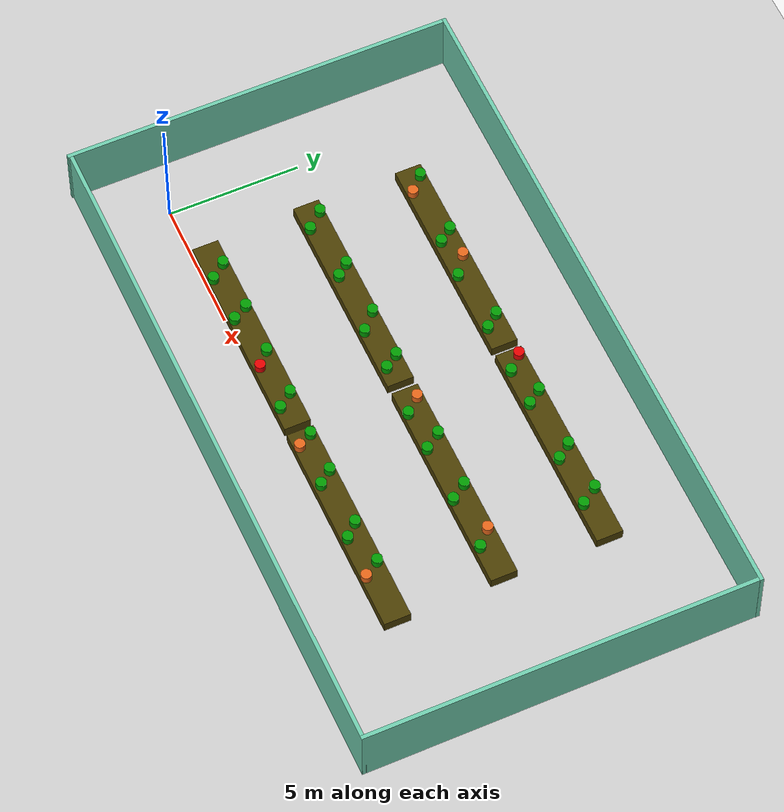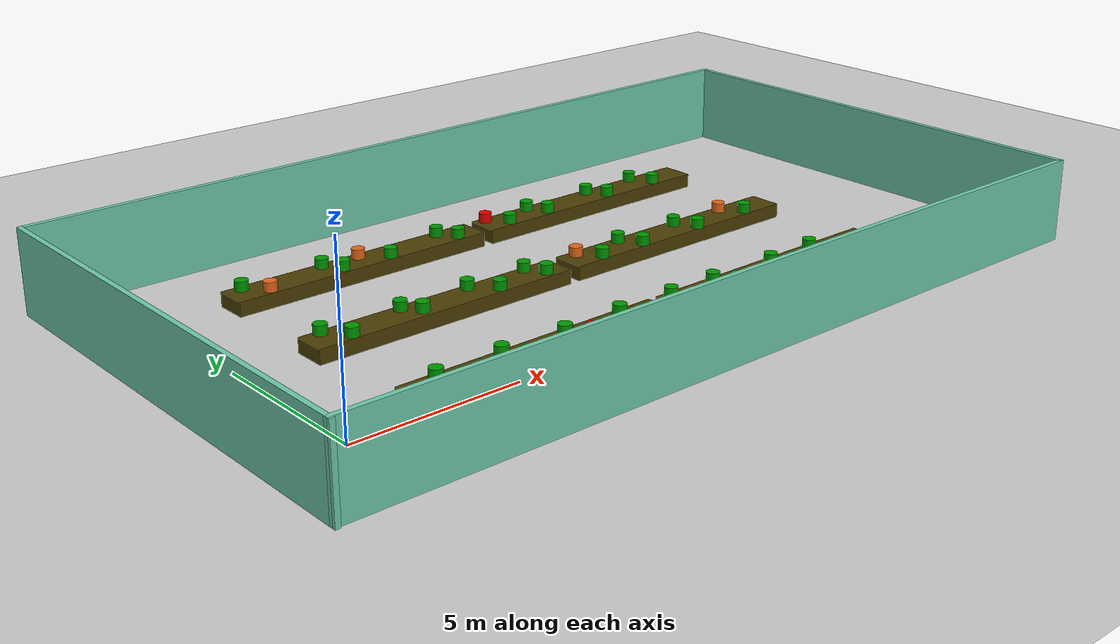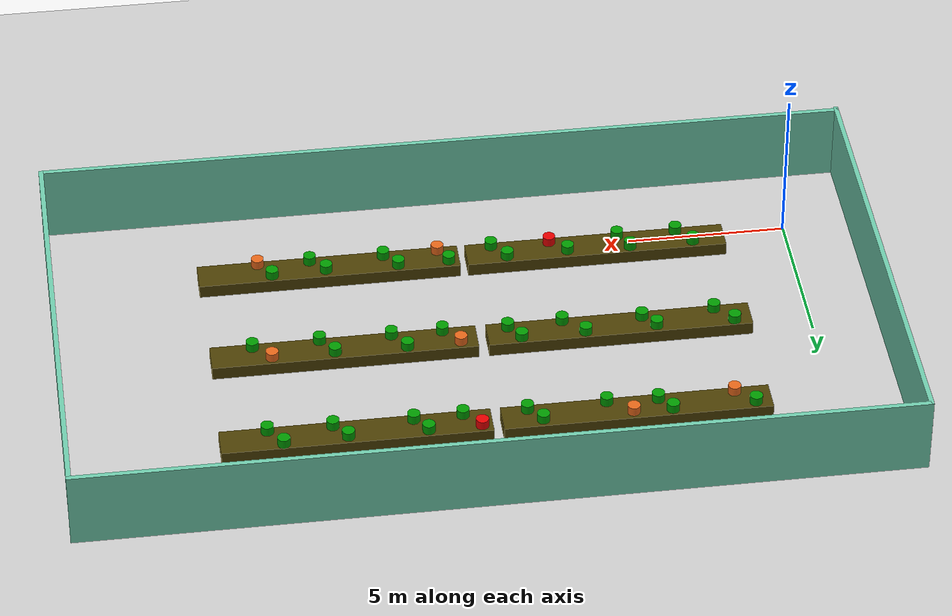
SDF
<sdf version="1.7">
 <world name="default">
  <light name="sun" type="directional">
   <pose>0 0 10 0 -0 0</pose>
   <diffuse>0.8 0.8 0.8 1</diffuse>
   <specular>0.2 0.2 0.2 1</specular>
   <attenuation>
    <range>1000</range>
    <constant>0.9</constant>
    <linear>0.01</linear>
    <quadratic>0.001</quadratic>
   </attenuation>
   <direction>-0.5 0.1 -0.9</direction>
   <spot><inner_angle>0</inner_angle><outer_angle>0</outer_angle><falloff>0</falloff></spot>
  </light>
  <model name="ground_plane">
   <static>1</static>
   <link name="link">
    <collision name="collision">
     <geometry><plane><normal>0 0 1</normal><size>100 100</size></plane></geometry>
     <surface><friction><ode><mu>100</mu><mu2>50</mu2></ode></friction></surface>
    </collision>
    <visual name="visual">
     <cast_shadows>0</cast_shadows>
     <geometry><plane><normal>0 0 1</normal><size>100 100</size></plane></geometry>
     <material>
      <script><uri>file://media/materials/scripts/gazebo.material</uri><name>Gazebo/Grey</name></script>
     </material>
    </visual>
   </link>
  </model>
  <gravity>0 0 -9.8</gravity>
  <magnetic_field>6e-06 2.3e-05 -4.2e-05</magnetic_field>
  <atmosphere type="adiabatic"/>
  <physics type="ode">
   <max_step_size>0.001</max_step_size>
   <real_time_factor>1</real_time_factor>
   <real_time_update_rate>1000</real_time_update_rate>
  </physics>
  <scene><ambient>0.4 0.4 0.4 1</ambient><background>0.7 0.7 0.7 1</background><shadows>1</shadows></scene>
  <spherical_coordinates>
   <surface_model>EARTH_WGS84</surface_model>
   <latitude_deg>0</latitude_deg>
   <longitude_deg>0</longitude_deg>
   <elevation>0</elevation>
   <heading_deg>0</heading_deg>
  </spherical_coordinates>
  <model name="Test_Bench_brown">
   <link name="link_1">
    <inertial>
     <mass>6.47546</mass>
     <inertia><ixx>0.639529</ixx><ixy>0</ixy><ixz>0</ixz><iyy>122.309</iyy><iyz>0</iyz><izz>122.749</izz></inertia>
    </inertial>
    <pose>0 4e-06 0 0 -0 0</pose>
    <visual name="visual">
     <geometry><box><size>8.26903 1 0.430283</size></box></geometry>
     <material>
      <lighting>1</lighting>
      <script><uri>file://media/materials/scripts/gazebo.material</uri><name>Gazebo/Grey</name></script>
      <shader type="pixel"><normal_map>__default__</normal_map></shader>
      <diffuse>0.298 0.247 0.016 1</diffuse>
      <ambient>0.3 0.3 0.3 1</ambient>
      <specular>0.01 0.01 0.01 1</specular>
      <emissive>0 0 0 1</emissive>
     </material>
    </visual>
    <collision name="collision">
     <geometry><box><size>8.26903 1 0.430283</size></box></geometry>
     <surface>
      <friction>
       <ode><mu>1</mu><mu2>1</mu2><fdir1>0 0 0</fdir1><slip1>0</slip1><slip2>0</slip2></ode>
       <torsional>
        <coefficient>1</coefficient>
        <patch_radius>0</patch_radius>
        <surface_radius>0</surface_radius>
        <use_patch_radius>1</use_patch_radius>
        <ode><slip>0</slip></ode>
       </torsional>
      </friction>
      <bounce><restitution_coefficient>0</restitution_coefficient><threshold>1e+06</threshold></bounce>
      <contact>
       <collide_without_contact>0</collide_without_contact>
       <collide_without_contact_bitmask>1</collide_without_contact_bitmask>
       <collide_bitmask>1</collide_bitmask>
       <ode>
        <soft_cfm>0</soft_cfm>
        <soft_erp>0.2</soft_erp>
        <kp>1e+13</kp>
        <kd>1</kd>
        <max_vel>0.01</max_vel>
        <min_depth>0</min_depth>
       </ode>
       <bullet>
        <split_impulse>1</split_impulse>
        <split_impulse_penetration_threshold>-0.01</split_impulse_penetration_threshold>
        <soft_cfm>0</soft_cfm>
        <soft_erp>0.2</soft_erp>
        <kp>1e+13</kp>
        <kd>1</kd>
       </bullet>
      </contact>
     </surface>
    </collision>
   </link>
   <static>0</static>
   <pose>6.16421 0.520482 0.215125 -1.4e-05 -0 1e-05</pose>
  </model>
  <model name="Test_Bench_brown_clone">
   <link name="link_1">
    <inertial>
     <mass>6.47546</mass>
     <inertia><ixx>0.639529</ixx><ixy>0</ixy><ixz>0</ixz><iyy>122.309</iyy><iyz>0</iyz><izz>122.749</izz></inertia>
    </inertial>
    <pose>0 4e-06 0 0 -0 0</pose>
    <visual name="visual">
     <geometry><box><size>8.26902 1 0.430283</size></box></geometry>
     <material>
      <lighting>1</lighting>
      <script><uri>file://media/materials/scripts/gazebo.material</uri><name>Gazebo/Grey</name></script>
      <shader type="pixel"><normal_map>__default__</normal_map></shader>
      <diffuse>0.298 0.247 0.016 1</diffuse>
      <ambient>0.3 0.3 0.3 1</ambient>
      <specular>0.01 0.01 0.01 1</specular>
      <emissive>0 0 0 1</emissive>
     </material>
    </visual>
    <collision name="collision">
     <geometry><box><size>8.26902 1 0.430283</size></box></geometry>
     <surface>
      <friction>
       <ode><mu>1</mu><mu2>1</mu2><fdir1>0 0 0</fdir1><slip1>0</slip1><slip2>0</slip2></ode>
       <torsional>
        <coefficient>1</coefficient>
        <patch_radius>0</patch_radius>
        <surface_radius>0</surface_radius>
        <use_patch_radius>1</use_patch_radius>
        <ode><slip>0</slip></ode>
       </torsional>
      </friction>
      <bounce><restitution_coefficient>0</restitution_coefficient><threshold>1e+06</threshold></bounce>
      <contact>
       <collide_without_contact>0</collide_without_contact>
       <collide_without_contact_bitmask>1</collide_without_contact_bitmask>
       <collide_bitmask>1</collide_bitmask>
       <ode>
        <soft_cfm>0</soft_cfm>
        <soft_erp>0.2</soft_erp>
        <kp>1e+13</kp>
        <kd>1</kd>
        <max_vel>0.01</max_vel>
        <min_depth>0</min_depth>
       </ode>
       <bullet>
        <split_impulse>1</split_impulse>
        <split_impulse_penetration_threshold>-0.01</split_impulse_penetration_threshold>
        <soft_cfm>0</soft_cfm>
        <soft_erp>0.2</soft_erp>
        <kp>1e+13</kp>
        <kd>1</kd>
       </bullet>
      </contact>
     </surface>
    </collision>
   </link>
   <static>0</static>
   <pose>14.6791 0.50719 0.213427 5.2e-05 -5e-06 -1e-05</pose>
  </model>
  <model name="Test_pot_green">
   <link name="link_0">
    <inertial>
     <mass>0.044841</mass>
     <inertia>
      <ixx>0.00074807</ixx>
      <ixy>0</ixy>
      <ixz>0</ixz>
      <iyy>0.00074807</iyy>
      <iyz>0</iyz>
      <izz>0.00086495</izz>
     </inertia>
    </inertial>
    <pose>3e-06 1e-06 0 0 -0 0</pose>
    <visual name="visual">
     <geometry><cylinder><radius>0.196415</radius><length>0.290612</length></cylinder></geometry>
     <material>
      <lighting>1</lighting>
      <script><uri>file://media/materials/scripts/gazebo.material</uri><name>Gazebo/Grey</name></script>
      <shader type="pixel"><normal_map>__default__</normal_map></shader>
      <diffuse>0 0.6 0 0</diffuse>
      <ambient>0.3 0.3 0.3 1</ambient>
      <specular>0.01 0.01 0.01 1</specular>
      <emissive>0 0 0 1</emissive>
     </material>
    </visual>
    <collision name="collision">
     <geometry><cylinder><radius>0.196415</radius><length>0.290612</length></cylinder></geometry>
     <surface>
      <friction>
       <ode><mu>1</mu><mu2>1</mu2><fdir1>0 0 0</fdir1><slip1>0</slip1><slip2>0</slip2></ode>
       <torsional>
        <coefficient>1</coefficient>
        <patch_radius>0</patch_radius>
        <surface_radius>0</surface_radius>
        <use_patch_radius>1</use_patch_radius>
        <ode><slip>0</slip></ode>
       </torsional>
      </friction>
      <bounce><restitution_coefficient>0</restitution_coefficient><threshold>1e+06</threshold></bounce>
      <contact>
       <collide_without_contact>0</collide_without_contact>
       <collide_without_contact_bitmask>1</collide_without_contact_bitmask>
       <collide_bitmask>1</collide_bitmask>
       <ode>
        <soft_cfm>0</soft_cfm>
        <soft_erp>0.2</soft_erp>
        <kp>1e+13</kp>
        <kd>1</kd>
        <max_vel>0.01</max_vel>
        <min_depth>0</min_depth>
       </ode>
       <bullet>
        <split_impulse>1</split_impulse>
        <split_impulse_penetration_threshold>-0.01</split_impulse_penetration_threshold>
        <soft_cfm>0</soft_cfm>
        <soft_erp>0.2</soft_erp>
        <kp>1e+13</kp>
        <kd>1</kd>
       </bullet>
      </contact>
     </surface>
    </collision>
   </link>
   <static>0</static>
   <pose>3.5522 0.210064 0.575581 6.3e-05 -8.7e-05 0.011992</pose>
  </model>
  <model name="Test_pot_red">
   <link name="link_0">
    <inertial>
     <mass>0.044841</mass>
     <inertia>
      <ixx>0.00074807</ixx>
      <ixy>0</ixy>
      <ixz>0</ixz>
      <iyy>0.00074807</iyy>
      <iyz>0</iyz>
      <izz>0.00086495</izz>
     </inertia>
    </inertial>
    <pose>3e-06 1e-06 -0 0 -0 0</pose>
    <visual name="visual">
     <geometry><cylinder><radius>0.196415</radius><length>0.290612</length></cylinder></geometry>
     <material>
      <lighting>1</lighting>
      <script><uri>file://media/materials/scripts/gazebo.material</uri><name>Gazebo/Grey</name></script>
      <shader type="pixel"><normal_map>__default__</normal_map></shader>
      <ambient>0.3 0.3 0.3 1</ambient>
      <diffuse>0.9 0 0 1</diffuse>
      <specular>0.01 0.01 0.01 1</specular>
      <emissive>0 0 0 1</emissive>
     </material>
    </visual>
    <collision name="collision">
     <geometry><cylinder><radius>0.196415</radius><length>0.290612</length></cylinder></geometry>
     <surface>
      <friction>
       <ode><mu>1</mu><mu2>1</mu2><fdir1>0 0 0</fdir1><slip1>0</slip1><slip2>0</slip2></ode>
       <torsional>
        <coefficient>1</coefficient>
        <patch_radius>0</patch_radius>
        <surface_radius>0</surface_radius>
        <use_patch_radius>1</use_patch_radius>
        <ode><slip>0</slip></ode>
       </torsional>
      </friction>
      <bounce><restitution_coefficient>0</restitution_coefficient><threshold>1e+06</threshold></bounce>
      <contact>
       <collide_without_contact>0</collide_without_contact>
       <collide_without_contact_bitmask>1</collide_without_contact_bitmask>
       <collide_bitmask>1</collide_bitmask>
       <ode>
        <soft_cfm>0</soft_cfm>
        <soft_erp>0.2</soft_erp>
        <kp>1e+13</kp>
        <kd>1</kd>
        <max_vel>0.01</max_vel>
        <min_depth>0</min_depth>
       </ode>
       <bullet>
        <split_impulse>1</split_impulse>
        <split_impulse_penetration_threshold>-0.01</split_impulse_penetration_threshold>
        <soft_cfm>0</soft_cfm>
        <soft_erp>0.2</soft_erp>
        <kp>1e+13</kp>
        <kd>1</kd>
       </bullet>
      </contact>
     </surface>
    </collision>
   </link>
   <static>0</static>
   <pose>7.62258 0.258837 0.575565 2.7e-05 0 0.006551</pose>
  </model>
  <model name="Test_pot_orange">
   <link name="link_0">
    <inertial>
     <mass>0.044841</mass>
     <inertia>
      <ixx>0.00074807</ixx>
      <ixy>0</ixy>
      <ixz>0</ixz>
      <iyy>0.00074807</iyy>
      <iyz>0</iyz>
      <izz>0.00086495</izz>
     </inertia>
    </inertial>
    <pose>3e-06 1e-06 -0 0 -0 0</pose>
    <visual name="visual">
     <geometry><cylinder><radius>0.196415</radius><length>0.290612</length></cylinder></geometry>
     <material>
      <lighting>1</lighting>
      <script><uri>file://media/materials/scripts/gazebo.material</uri><name>Gazebo/Grey</name></script>
      <shader type="pixel"><normal_map>__default__</normal_map></shader>
      <ambient>0.3 0.3 0.3 1</ambient>
      <diffuse>0.9 0.4 0.1 1</diffuse>
      <specular>0.01 0.01 0.01 1</specular>
      <emissive>0 0 0 1</emissive>
     </material>
    </visual>
    <collision name="collision">
     <geometry><cylinder><radius>0.196415</radius><length>0.290612</length></cylinder></geometry>
     <surface>
      <friction>
       <ode><mu>1</mu><mu2>1</mu2><fdir1>0 0 0</fdir1><slip1>0</slip1><slip2>0</slip2></ode>
       <torsional>
        <coefficient>1</coefficient>
        <patch_radius>0</patch_radius>
        <surface_radius>0</surface_radius>
        <use_patch_radius>1</use_patch_radius>
        <ode><slip>0</slip></ode>
       </torsional>
      </friction>
      <bounce><restitution_coefficient>0</restitution_coefficient><threshold>1e+06</threshold></bounce>
      <contact>
       <collide_without_contact>0</collide_without_contact>
       <collide_without_contact_bitmask>1</collide_without_contact_bitmask>
       <collide_bitmask>1</collide_bitmask>
       <ode>
        <soft_cfm>0</soft_cfm>
        <soft_erp>0.2</soft_erp>
        <kp>1e+13</kp>
        <kd>1</kd>
        <max_vel>0.01</max_vel>
        <min_depth>0</min_depth>
       </ode>
       <bullet>
        <split_impulse>1</split_impulse>
        <split_impulse_penetration_threshold>-0.01</split_impulse_penetration_threshold>
        <soft_cfm>0</soft_cfm>
        <soft_erp>0.2</soft_erp>
        <kp>1e+13</kp>
        <kd>1</kd>
       </bullet>
      </contact>
     </surface>
    </collision>
   </link>
   <static>0</static>
   <pose>11.1966 0.219359 0.57385 9.3e-05 -8e-06 0.011416</pose>
  </model>
  <model name="Test_Bench_brown_clone_0">
   <link name="link_1">
    <inertial>
     <mass>6.47546</mass>
     <inertia><ixx>0.639529</ixx><ixy>0</ixy><ixz>0</ixz><iyy>122.309</iyy><iyz>0</iyz><izz>122.749</izz></inertia>
    </inertial>
    <pose>0 4e-06 0 0 -0 0</pose>
    <visual name="visual">
     <geometry><box><size>8.26902 1 0.430283</size></box></geometry>
     <material>
      <lighting>1</lighting>
      <script><uri>file://media/materials/scripts/gazebo.material</uri><name>Gazebo/Grey</name></script>
      <shader type="pixel"><normal_map>__default__</normal_map></shader>
      <diffuse>0.298 0.247 0.016 1</diffuse>
      <ambient>0.3 0.3 0.3 1</ambient>
      <specular>0.01 0.01 0.01 1</specular>
      <emissive>0 0 0 1</emissive>
     </material>
    </visual>
    <collision name="collision">
     <geometry><box><size>8.26902 1 0.430283</size></box></geometry>
     <surface>
      <friction>
       <ode><mu>1</mu><mu2>1</mu2><fdir1>0 0 0</fdir1><slip1>0</slip1><slip2>0</slip2></ode>
       <torsional>
        <coefficient>1</coefficient>
        <patch_radius>0</patch_radius>
        <surface_radius>0</surface_radius>
        <use_patch_radius>1</use_patch_radius>
        <ode><slip>0</slip></ode>
       </torsional>
      </friction>
      <bounce><restitution_coefficient>0</restitution_coefficient><threshold>1e+06</threshold></bounce>
      <contact>
       <collide_without_contact>0</collide_without_contact>
       <collide_without_contact_bitmask>1</collide_without_contact_bitmask>
       <collide_bitmask>1</collide_bitmask>
       <ode>
        <soft_cfm>0</soft_cfm>
        <soft_erp>0.2</soft_erp>
        <kp>1e+13</kp>
        <kd>1</kd>
        <max_vel>0.01</max_vel>
        <min_depth>0</min_depth>
       </ode>
       <bullet>
        <split_impulse>1</split_impulse>
        <split_impulse_penetration_threshold>-0.01</split_impulse_penetration_threshold>
        <soft_cfm>0</soft_cfm>
        <soft_erp>0.2</soft_erp>
        <kp>1e+13</kp>
        <kd>1</kd>
       </bullet>
      </contact>
     </surface>
    </collision>
   </link>
   <static>0</static>
   <pose>6.02902 4.51582 0.210183 0.000215 -1.1e-05 2e-06</pose>
  </model>
  <model name="Test_Bench_brown_clone_1">
   <link name="link_1">
    <inertial>
     <mass>6.47546</mass>
     <inertia><ixx>0.639529</ixx><ixy>0</ixy><ixz>0</ixz><iyy>122.309</iyy><iyz>0</iyz><izz>122.749</izz></inertia>
    </inertial>
    <pose>0 4e-06 0 0 -0 0</pose>
    <visual name="visual">
     <geometry><box><size>8.26902 1 0.430283</size></box></geometry>
     <material>
      <lighting>1</lighting>
      <script><uri>file://media/materials/scripts/gazebo.material</uri><name>Gazebo/Grey</name></script>
      <shader type="pixel"><normal_map>__default__</normal_map></shader>
      <diffuse>0.298 0.247 0.016 1</diffuse>
      <ambient>0.3 0.3 0.3 1</ambient>
      <specular>0.01 0.01 0.01 1</specular>
      <emissive>0 0 0 1</emissive>
     </material>
    </visual>
    <collision name="collision">
     <geometry><box><size>8.26902 1 0.430283</size></box></geometry>
     <surface>
      <friction>
       <ode><mu>1</mu><mu2>1</mu2><fdir1>0 0 0</fdir1><slip1>0</slip1><slip2>0</slip2></ode>
       <torsional>
        <coefficient>1</coefficient>
        <patch_radius>0</patch_radius>
        <surface_radius>0</surface_radius>
        <use_patch_radius>1</use_patch_radius>
        <ode><slip>0</slip></ode>
       </torsional>
      </friction>
      <bounce><restitution_coefficient>0</restitution_coefficient><threshold>1e+06</threshold></bounce>
      <contact>
       <collide_without_contact>0</collide_without_contact>
       <collide_without_contact_bitmask>1</collide_without_contact_bitmask>
       <collide_bitmask>1</collide_bitmask>
       <ode>
        <soft_cfm>0</soft_cfm>
        <soft_erp>0.2</soft_erp>
        <kp>1e+13</kp>
        <kd>1</kd>
        <max_vel>0.01</max_vel>
        <min_depth>0</min_depth>
       </ode>
       <bullet>
        <split_impulse>1</split_impulse>
        <split_impulse_penetration_threshold>-0.01</split_impulse_penetration_threshold>
        <soft_cfm>0</soft_cfm>
        <soft_erp>0.2</soft_erp>
        <kp>1e+13</kp>
        <kd>1</kd>
       </bullet>
      </contact>
     </surface>
    </collision>
   </link>
   <static>0</static>
   <pose>14.6227 4.52237 0.215141 0 -0 0</pose>
  </model>
  <model name="Test_Bench_brown_clone_2">
   <link name="link_1">
    <inertial>
     <mass>6.47546</mass>
     <inertia><ixx>0.639529</ixx><ixy>0</ixy><ixz>0</ixz><iyy>122.309</iyy><iyz>0</iyz><izz>122.749</izz></inertia>
    </inertial>
    <pose>0 4e-06 0 0 -0 0</pose>
    <visual name="visual">
     <geometry><box><size>8.26902 1 0.430283</size></box></geometry>
     <material>
      <lighting>1</lighting>
      <script><uri>file://media/materials/scripts/gazebo.material</uri><name>Gazebo/Grey</name></script>
      <shader type="pixel"><normal_map>__default__</normal_map></shader>
      <diffuse>0.298 0.247 0.016 1</diffuse>
      <ambient>0.3 0.3 0.3 1</ambient>
      <specular>0.01 0.01 0.01 1</specular>
      <emissive>0 0 0 1</emissive>
     </material>
    </visual>
    <collision name="collision">
     <geometry><box><size>8.26902 1 0.430283</size></box></geometry>
     <surface>
      <friction>
       <ode><mu>1</mu><mu2>1</mu2><fdir1>0 0 0</fdir1><slip1>0</slip1><slip2>0</slip2></ode>
       <torsional>
        <coefficient>1</coefficient>
        <patch_radius>0</patch_radius>
        <surface_radius>0</surface_radius>
        <use_patch_radius>1</use_patch_radius>
        <ode><slip>0</slip></ode>
       </torsional>
      </friction>
      <bounce><restitution_coefficient>0</restitution_coefficient><threshold>1e+06</threshold></bounce>
      <contact>
       <collide_without_contact>0</collide_without_contact>
       <collide_without_contact_bitmask>1</collide_without_contact_bitmask>
       <collide_bitmask>1</collide_bitmask>
       <ode>
        <soft_cfm>0</soft_cfm>
        <soft_erp>0.2</soft_erp>
        <kp>1e+13</kp>
        <kd>1</kd>
        <max_vel>0.01</max_vel>
        <min_depth>0</min_depth>
       </ode>
       <bullet>
        <split_impulse>1</split_impulse>
        <split_impulse_penetration_threshold>-0.01</split_impulse_penetration_threshold>
        <soft_cfm>0</soft_cfm>
        <soft_erp>0.2</soft_erp>
        <kp>1e+13</kp>
        <kd>1</kd>
       </bullet>
      </contact>
     </surface>
    </collision>
   </link>
   <static>0</static>
   <pose>6.11341 8.4951 0.215141 0 -0 -3e-06</pose>
  </model>
  <model name="Test_Bench_brown_clone_3">
   <link name="link_1">
    <inertial>
     <mass>6.47546</mass>
     <inertia><ixx>0.639529</ixx><ixy>0</ixy><ixz>0</ixz><iyy>122.309</iyy><iyz>0</iyz><izz>122.749</izz></inertia>
    </inertial>
    <pose>0 4e-06 0 0 -0 0</pose>
    <visual name="visual">
     <geometry><box><size>8.26902 1 0.430283</size></box></geometry>
     <material>
      <lighting>1</lighting>
      <script><uri>file://media/materials/scripts/gazebo.material</uri><name>Gazebo/Grey</name></script>
      <shader type="pixel"><normal_map>__default__</normal_map></shader>
      <diffuse>0.298 0.247 0.016 1</diffuse>
      <ambient>0.3 0.3 0.3 1</ambient>
      <specular>0.01 0.01 0.01 1</specular>
      <emissive>0 0 0 1</emissive>
     </material>
    </visual>
    <collision name="collision">
     <geometry><box><size>8.26902 1 0.430283</size></box></geometry>
     <surface>
      <friction>
       <ode><mu>1</mu><mu2>1</mu2><fdir1>0 0 0</fdir1><slip1>0</slip1><slip2>0</slip2></ode>
       <torsional>
        <coefficient>1</coefficient>
        <patch_radius>0</patch_radius>
        <surface_radius>0</surface_radius>
        <use_patch_radius>1</use_patch_radius>
        <ode><slip>0</slip></ode>
       </torsional>
      </friction>
      <bounce><restitution_coefficient>0</restitution_coefficient><threshold>1e+06</threshold></bounce>
      <contact>
       <collide_without_contact>0</collide_without_contact>
       <collide_without_contact_bitmask>1</collide_without_contact_bitmask>
       <collide_bitmask>1</collide_bitmask>
       <ode>
        <soft_cfm>0</soft_cfm>
        <soft_erp>0.2</soft_erp>
        <kp>1e+13</kp>
        <kd>1</kd>
        <max_vel>0.01</max_vel>
        <min_depth>0</min_depth>
       </ode>
       <bullet>
        <split_impulse>1</split_impulse>
        <split_impulse_penetration_threshold>-0.01</split_impulse_penetration_threshold>
        <soft_cfm>0</soft_cfm>
        <soft_erp>0.2</soft_erp>
        <kp>1e+13</kp>
        <kd>1</kd>
       </bullet>
      </contact>
     </surface>
    </collision>
   </link>
   <static>0</static>
   <pose>14.6865 8.49522 0.21379 5.3e-05 -3e-06 8e-06</pose>
  </model>
  <model name="walls3">
   <link name="Wall_10">
    <pose>12.8059 -2.49306 0 0 -0 1.5708</pose>
    <inertial>
     <inertia><ixx>0</ixx><ixy>0</ixy><ixz>0</ixz><iyy>0</iyy><iyz>0</iyz><izz>0</izz></inertia>
     <mass>0</mass>
    </inertial>
    <visual name="Wall_10_Visual">
     <pose>0 0 1.25 0 -0 0</pose>
     <geometry><box><size>14.709 0.15 2.5</size></box></geometry>
     <material>
      <script><uri>file://media/materials/scripts/gazebo.material</uri><name>Gazebo/Grey</name></script>
      <ambient>0.435294 0.796078 0.67451 1</ambient>
      <shader type="pixel"/>
     </material>
     <meta><layer>0</layer></meta>
    </visual>
    <collision name="Wall_10_Collision">
     <pose>0 0 1.25 0 -0 0</pose>
     <geometry><box><size>14.709 0.15 2.5</size></box></geometry>
     <surface>
      <friction>
       <ode><mu>1</mu><mu2>1</mu2><fdir1>0 0 0</fdir1><slip1>0</slip1><slip2>0</slip2></ode>
       <torsional>
        <coefficient>1</coefficient>
        <patch_radius>0</patch_radius>
        <surface_radius>0</surface_radius>
        <use_patch_radius>1</use_patch_radius>
        <ode><slip>0</slip></ode>
       </torsional>
      </friction>
      <bounce><restitution_coefficient>0</restitution_coefficient><threshold>1e+06</threshold></bounce>
      <contact>
       <collide_without_contact>0</collide_without_contact>
       <collide_without_contact_bitmask>1</collide_without_contact_bitmask>
       <collide_bitmask>1</collide_bitmask>
       <ode>
        <soft_cfm>0</soft_cfm>
        <soft_erp>0.2</soft_erp>
        <kp>1e+13</kp>
        <kd>1</kd>
        <max_vel>0.01</max_vel>
        <min_depth>0</min_depth>
       </ode>
       <bullet>
        <split_impulse>1</split_impulse>
        <split_impulse_penetration_threshold>-0.01</split_impulse_penetration_threshold>
        <soft_cfm>0</soft_cfm>
        <soft_erp>0.2</soft_erp>
        <kp>1e+13</kp>
        <kd>1</kd>
       </bullet>
      </contact>
     </surface>
    </collision>
   </link>
   <link name="Wall_12">
    <pose>0.013351 4.87054 0 0 -0 0</pose>
    <inertial>
     <inertia><ixx>0</ixx><ixy>0</ixy><ixz>0</ixz><iyy>0</iyy><iyz>0</iyz><izz>0</izz></inertia>
     <mass>0</mass>
    </inertial>
    <visual name="Wall_12_Visual">
     <pose>0 0 1.25 0 -0 0</pose>
     <geometry><box><size>25.75 0.15 2.5</size></box></geometry>
     <material>
      <script><uri>file://media/materials/scripts/gazebo.material</uri><name>Gazebo/Grey</name></script>
      <ambient>0.435294 0.796078 0.67451 1</ambient>
      <shader type="pixel"/>
     </material>
     <meta><layer>0</layer></meta>
    </visual>
    <collision name="Wall_12_Collision">
     <pose>0 0 1.25 0 -0 0</pose>
     <geometry><box><size>25.75 0.15 2.5</size></box></geometry>
     <surface>
      <friction>
       <ode><mu>1</mu><mu2>1</mu2><fdir1>0 0 0</fdir1><slip1>0</slip1><slip2>0</slip2></ode>
       <torsional>
        <coefficient>1</coefficient>
        <patch_radius>0</patch_radius>
        <surface_radius>0</surface_radius>
        <use_patch_radius>1</use_patch_radius>
        <ode><slip>0</slip></ode>
       </torsional>
      </friction>
      <bounce><restitution_coefficient>0</restitution_coefficient><threshold>1e+06</threshold></bounce>
      <contact>
       <collide_without_contact>0</collide_without_contact>
       <collide_without_contact_bitmask>1</collide_without_contact_bitmask>
       <collide_bitmask>1</collide_bitmask>
       <ode>
        <soft_cfm>0</soft_cfm>
        <soft_erp>0.2</soft_erp>
        <kp>1e+13</kp>
        <kd>1</kd>
        <max_vel>0.01</max_vel>
        <min_depth>0</min_depth>
       </ode>
       <bullet>
        <split_impulse>1</split_impulse>
        <split_impulse_penetration_threshold>-0.01</split_impulse_penetration_threshold>
        <soft_cfm>0</soft_cfm>
        <soft_erp>0.2</soft_erp>
        <kp>1e+13</kp>
        <kd>1</kd>
       </bullet>
      </contact>
     </surface>
    </collision>
   </link>
   <link name="Wall_6">
    <pose>-12.8033 -2.47448 0 0 0 -1.57216</pose>
    <inertial>
     <inertia><ixx>0</ixx><ixy>0</ixy><ixz>0</ixz><iyy>0</iyy><iyz>0</iyz><izz>0</izz></inertia>
     <mass>0</mass>
    </inertial>
    <visual name="Wall_6_Visual">
     <pose>0 0 1.25 0 -0 0</pose>
     <geometry><box><size>14.8095 0.15 2.5</size></box></geometry>
     <material>
      <script><uri>file://media/materials/scripts/gazebo.material</uri><name>Gazebo/Grey</name></script>
      <ambient>0.435294 0.796078 0.67451 1</ambient>
      <shader type="pixel"/>
     </material>
     <meta><layer>0</layer></meta>
    </visual>
    <collision name="Wall_6_Collision">
     <pose>0 0 1.25 0 -0 0</pose>
     <geometry><box><size>14.8095 0.15 2.5</size></box></geometry>
     <surface>
      <friction>
       <ode><mu>1</mu><mu2>1</mu2><fdir1>0 0 0</fdir1><slip1>0</slip1><slip2>0</slip2></ode>
       <torsional>
        <coefficient>1</coefficient>
        <patch_radius>0</patch_radius>
        <surface_radius>0</surface_radius>
        <use_patch_radius>1</use_patch_radius>
        <ode><slip>0</slip></ode>
       </torsional>
      </friction>
      <bounce><restitution_coefficient>0</restitution_coefficient><threshold>1e+06</threshold></bounce>
      <contact>
       <collide_without_contact>0</collide_without_contact>
       <collide_without_contact_bitmask>1</collide_without_contact_bitmask>
       <collide_bitmask>1</collide_bitmask>
       <ode>
        <soft_cfm>0</soft_cfm>
        <soft_erp>0.2</soft_erp>
        <kp>1e+13</kp>
        <kd>1</kd>
        <max_vel>0.01</max_vel>
        <min_depth>0</min_depth>
       </ode>
       <bullet>
        <split_impulse>1</split_impulse>
        <split_impulse_penetration_threshold>-0.01</split_impulse_penetration_threshold>
        <soft_cfm>0</soft_cfm>
        <soft_erp>0.2</soft_erp>
        <kp>1e+13</kp>
        <kd>1</kd>
       </bullet>
      </contact>
     </surface>
    </collision>
   </link>
   <link name="Wall_8">
    <pose>-0.003688 -9.7616 0 0 0 -0.001038</pose>
    <visual name="Wall_8_Visual">
     <pose>0 0 1.25 0 -0 0</pose>
     <geometry><box><size>25.7691 0.15 2.5</size></box></geometry>
     <material>
      <script><uri>file://media/materials/scripts/gazebo.material</uri><name>Gazebo/Grey</name></script>
      <ambient>0.435294 0.796078 0.67451 1</ambient>
      <shader type="pixel"/>
     </material>
     <meta><layer>0</layer></meta>
    </visual>
    <collision name="Wall_8_Collision">
     <pose>0 0 1.25 0 -0 0</pose>
     <geometry><box><size>25.7691 0.15 2.5</size></box></geometry>
     <surface>
      <friction>
       <ode><mu>1</mu><mu2>1</mu2><fdir1>0 0 0</fdir1><slip1>0</slip1><slip2>0</slip2></ode>
       <torsional>
        <coefficient>1</coefficient>
        <patch_radius>0</patch_radius>
        <surface_radius>0</surface_radius>
        <use_patch_radius>1</use_patch_radius>
        <ode><slip>0</slip></ode>
       </torsional>
      </friction>
      <bounce><restitution_coefficient>0</restitution_coefficient><threshold>1e+06</threshold></bounce>
      <contact>
       <collide_without_contact>0</collide_without_contact>
       <collide_without_contact_bitmask>1</collide_without_contact_bitmask>
       <collide_bitmask>1</collide_bitmask>
       <ode>
        <soft_cfm>0</soft_cfm>
        <soft_erp>0.2</soft_erp>
        <kp>1e+13</kp>
        <kd>1</kd>
        <max_vel>0.01</max_vel>
        <min_depth>0</min_depth>
       </ode>
       <bullet>
        <split_impulse>1</split_impulse>
        <split_impulse_penetration_threshold>-0.01</split_impulse_penetration_threshold>
        <soft_cfm>0</soft_cfm>
        <soft_erp>0.2</soft_erp>
        <kp>1e+13</kp>
        <kd>1</kd>
       </bullet>
      </contact>
     </surface>
    </collision>
   </link>
   <static>1</static>
   <pose>10.639 6.94407 0 0 -0 0</pose>
  </model>
  <model name="Test_pot_orange_clone">
   <link name="link_0">
    <inertial>
     <mass>0.044841</mass>
     <inertia>
      <ixx>0.00074807</ixx>
      <ixy>0</ixy>
      <ixz>0</ixz>
      <iyy>0.00074807</iyy>
      <iyz>0</iyz>
      <izz>0.00086495</izz>
     </inertia>
    </inertial>
    <pose>3e-06 1e-06 -0 0 -0 0</pose>
    <visual name="visual">
     <geometry><cylinder><radius>0.196415</radius><length>0.290612</length></cylinder></geometry>
     <material>
      <lighting>1</lighting>
      <script><uri>file://media/materials/scripts/gazebo.material</uri><name>Gazebo/Grey</name></script>
      <shader type="pixel"><normal_map>__default__</normal_map></shader>
      <ambient>0.3 0.3 0.3 1</ambient>
      <diffuse>0.9 0.4 0.1 1</diffuse>
      <specular>0.01 0.01 0.01 1</specular>
      <emissive>0 0 0 1</emissive>
     </material>
    </visual>
    <collision name="collision">
     <geometry><cylinder><radius>0.196415</radius><length>0.290612</length></cylinder></geometry>
     <surface>
      <friction>
       <ode><mu>1</mu><mu2>1</mu2><fdir1>0 0 0</fdir1><slip1>0</slip1><slip2>0</slip2></ode>
       <torsional>
        <coefficient>1</coefficient>
        <patch_radius>0</patch_radius>
        <surface_radius>0</surface_radius>
        <use_patch_radius>1</use_patch_radius>
        <ode><slip>0</slip></ode>
       </torsional>
      </friction>
      <bounce><restitution_coefficient>0</restitution_coefficient><threshold>1e+06</threshold></bounce>
      <contact>
       <collide_without_contact>0</collide_without_contact>
       <collide_without_contact_bitmask>1</collide_without_contact_bitmask>
       <collide_bitmask>1</collide_bitmask>
       <ode>
        <soft_cfm>0</soft_cfm>
        <soft_erp>0.2</soft_erp>
        <kp>1e+13</kp>
        <kd>1</kd>
        <max_vel>0.01</max_vel>
        <min_depth>0</min_depth>
       </ode>
       <bullet>
        <split_impulse>1</split_impulse>
        <split_impulse_penetration_threshold>-0.01</split_impulse_penetration_threshold>
        <soft_cfm>0</soft_cfm>
        <soft_erp>0.2</soft_erp>
        <kp>1e+13</kp>
        <kd>1</kd>
       </bullet>
      </contact>
     </surface>
    </collision>
   </link>
   <static>0</static>
   <pose>16.9073 0.195438 0.575586 -1.3e-05 8e-06 0.003965</pose>
  </model>
  <model name="Test_pot_green_clone">
   <link name="link_0">
    <inertial>
     <mass>0.044841</mass>
     <inertia>
      <ixx>0.00074807</ixx>
      <ixy>0</ixy>
      <ixz>0</ixz>
      <iyy>0.00074807</iyy>
      <iyz>0</iyz>
      <izz>0.00086495</izz>
     </inertia>
    </inertial>
    <pose>3e-06 1e-06 0 0 -0 0</pose>
    <visual name="visual">
     <geometry><cylinder><radius>0.196415</radius><length>0.290612</length></cylinder></geometry>
     <material>
      <lighting>1</lighting>
      <script><uri>file://media/materials/scripts/gazebo.material</uri><name>Gazebo/Grey</name></script>
      <shader type="pixel"><normal_map>__default__</normal_map></shader>
      <diffuse>0 0.6 0 0</diffuse>
      <ambient>0.3 0.3 0.3 1</ambient>
      <specular>0.01 0.01 0.01 1</specular>
      <emissive>0 0 0 1</emissive>
     </material>
    </visual>
    <collision name="collision">
     <geometry><cylinder><radius>0.196415</radius><length>0.290612</length></cylinder></geometry>
     <surface>
      <friction>
       <ode><mu>1</mu><mu2>1</mu2><fdir1>0 0 0</fdir1><slip1>0</slip1><slip2>0</slip2></ode>
       <torsional>
        <coefficient>1</coefficient>
        <patch_radius>0</patch_radius>
        <surface_radius>0</surface_radius>
        <use_patch_radius>1</use_patch_radius>
        <ode><slip>0</slip></ode>
       </torsional>
      </friction>
      <bounce><restitution_coefficient>0</restitution_coefficient><threshold>1e+06</threshold></bounce>
      <contact>
       <collide_without_contact>0</collide_without_contact>
       <collide_without_contact_bitmask>1</collide_without_contact_bitmask>
       <collide_bitmask>1</collide_bitmask>
       <ode>
        <soft_cfm>0</soft_cfm>
        <soft_erp>0.2</soft_erp>
        <kp>1e+13</kp>
        <kd>1</kd>
        <max_vel>0.01</max_vel>
        <min_depth>0</min_depth>
       </ode>
       <bullet>
        <split_impulse>1</split_impulse>
        <split_impulse_penetration_threshold>-0.01</split_impulse_penetration_threshold>
        <soft_cfm>0</soft_cfm>
        <soft_erp>0.2</soft_erp>
        <kp>1e+13</kp>
        <kd>1</kd>
       </bullet>
      </contact>
     </surface>
    </collision>
   </link>
   <static>0</static>
   <pose>3.00083 4.20327 0.570529 0.000259 -1.5e-05 0.007801</pose>
  </model>
  <model name="Test_pot_green_clone_0">
   <link name="link_0">
    <inertial>
     <mass>0.044841</mass>
     <inertia>
      <ixx>0.00074807</ixx>
      <ixy>0</ixy>
      <ixz>0</ixz>
      <iyy>0.00074807</iyy>
      <iyz>0</iyz>
      <izz>0.00086495</izz>
     </inertia>
    </inertial>
    <pose>3e-06 1e-06 0 0 -0 0</pose>
    <visual name="visual">
     <geometry><cylinder><radius>0.196415</radius><length>0.290612</length></cylinder></geometry>
     <material>
      <lighting>1</lighting>
      <script><uri>file://media/materials/scripts/gazebo.material</uri><name>Gazebo/Grey</name></script>
      <shader type="pixel"><normal_map>__default__</normal_map></shader>
      <diffuse>0 0.6 0 0</diffuse>
      <ambient>0.3 0.3 0.3 1</ambient>
      <specular>0.01 0.01 0.01 1</specular>
      <emissive>0 0 0 1</emissive>
     </material>
    </visual>
    <collision name="collision">
     <geometry><cylinder><radius>0.196415</radius><length>0.290612</length></cylinder></geometry>
     <surface>
      <friction>
       <ode><mu>1</mu><mu2>1</mu2><fdir1>0 0 0</fdir1><slip1>0</slip1><slip2>0</slip2></ode>
       <torsional>
        <coefficient>1</coefficient>
        <patch_radius>0</patch_radius>
        <surface_radius>0</surface_radius>
        <use_patch_radius>1</use_patch_radius>
        <ode><slip>0</slip></ode>
       </torsional>
      </friction>
      <bounce><restitution_coefficient>0</restitution_coefficient><threshold>1e+06</threshold></bounce>
      <contact>
       <collide_without_contact>0</collide_without_contact>
       <collide_without_contact_bitmask>1</collide_without_contact_bitmask>
       <collide_bitmask>1</collide_bitmask>
       <ode>
        <soft_cfm>0</soft_cfm>
        <soft_erp>0.2</soft_erp>
        <kp>1e+13</kp>
        <kd>1</kd>
        <max_vel>0.01</max_vel>
        <min_depth>0</min_depth>
       </ode>
       <bullet>
        <split_impulse>1</split_impulse>
        <split_impulse_penetration_threshold>-0.01</split_impulse_penetration_threshold>
        <soft_cfm>0</soft_cfm>
        <soft_erp>0.2</soft_erp>
        <kp>1e+13</kp>
        <kd>1</kd>
       </bullet>
      </contact>
     </surface>
    </collision>
   </link>
   <static>0</static>
   <pose>7.78114 4.20143 0.575591 0 -1.1e-05 0.003268</pose>
  </model>
  <model name="Test_pot_green_clone_1">
   <link name="link_0">
    <inertial>
     <mass>0.044841</mass>
     <inertia>
      <ixx>0.00074807</ixx>
      <ixy>0</ixy>
      <ixz>0</ixz>
      <iyy>0.00074807</iyy>
      <iyz>0</iyz>
      <izz>0.00086495</izz>
     </inertia>
    </inertial>
    <pose>3e-06 1e-06 0 0 -0 0</pose>
    <visual name="visual">
     <geometry><cylinder><radius>0.196415</radius><length>0.290612</length></cylinder></geometry>
     <material>
      <lighting>1</lighting>
      <script><uri>file://media/materials/scripts/gazebo.material</uri><name>Gazebo/Grey</name></script>
      <shader type="pixel"><normal_map>__default__</normal_map></shader>
      <diffuse>0 0.6 0 0</diffuse>
      <ambient>0.3 0.3 0.3 1</ambient>
      <specular>0.01 0.01 0.01 1</specular>
      <emissive>0 0 0 1</emissive>
     </material>
    </visual>
    <collision name="collision">
     <geometry><cylinder><radius>0.196415</radius><length>0.290612</length></cylinder></geometry>
     <surface>
      <friction>
       <ode><mu>1</mu><mu2>1</mu2><fdir1>0 0 0</fdir1><slip1>0</slip1><slip2>0</slip2></ode>
       <torsional>
        <coefficient>1</coefficient>
        <patch_radius>0</patch_radius>
        <surface_radius>0</surface_radius>
        <use_patch_radius>1</use_patch_radius>
        <ode><slip>0</slip></ode>
       </torsional>
      </friction>
      <bounce><restitution_coefficient>0</restitution_coefficient><threshold>1e+06</threshold></bounce>
      <contact>
       <collide_without_contact>0</collide_without_contact>
       <collide_without_contact_bitmask>1</collide_without_contact_bitmask>
       <collide_bitmask>1</collide_bitmask>
       <ode>
        <soft_cfm>0</soft_cfm>
        <soft_erp>0.2</soft_erp>
        <kp>1e+13</kp>
        <kd>1</kd>
        <max_vel>0.01</max_vel>
        <min_depth>0</min_depth>
       </ode>
       <bullet>
        <split_impulse>1</split_impulse>
        <split_impulse_penetration_threshold>-0.01</split_impulse_penetration_threshold>
        <soft_cfm>0</soft_cfm>
        <soft_erp>0.2</soft_erp>
        <kp>1e+13</kp>
        <kd>1</kd>
       </bullet>
      </contact>
     </surface>
    </collision>
   </link>
   <static>0</static>
   <pose>11.5309 4.19869 0.575589 -1e-06 -0 0.01172</pose>
  </model>
  <model name="Test_pot_green_clone_2">
   <link name="link_0">
    <inertial>
     <mass>0.044841</mass>
     <inertia>
      <ixx>0.00074807</ixx>
      <ixy>0</ixy>
      <ixz>0</ixz>
      <iyy>0.00074807</iyy>
      <iyz>0</iyz>
      <izz>0.00086495</izz>
     </inertia>
    </inertial>
    <pose>3e-06 1e-06 0 0 -0 0</pose>
    <visual name="visual">
     <geometry><cylinder><radius>0.196415</radius><length>0.290612</length></cylinder></geometry>
     <material>
      <lighting>1</lighting>
      <script><uri>file://media/materials/scripts/gazebo.material</uri><name>Gazebo/Grey</name></script>
      <shader type="pixel"><normal_map>__default__</normal_map></shader>
      <diffuse>0 0.6 0 0</diffuse>
      <ambient>0.3 0.3 0.3 1</ambient>
      <specular>0.01 0.01 0.01 1</specular>
      <emissive>0 0 0 1</emissive>
     </material>
    </visual>
    <collision name="collision">
     <geometry><cylinder><radius>0.196415</radius><length>0.290612</length></cylinder></geometry>
     <surface>
      <friction>
       <ode><mu>1</mu><mu2>1</mu2><fdir1>0 0 0</fdir1><slip1>0</slip1><slip2>0</slip2></ode>
       <torsional>
        <coefficient>1</coefficient>
        <patch_radius>0</patch_radius>
        <surface_radius>0</surface_radius>
        <use_patch_radius>1</use_patch_radius>
        <ode><slip>0</slip></ode>
       </torsional>
      </friction>
      <bounce><restitution_coefficient>0</restitution_coefficient><threshold>1e+06</threshold></bounce>
      <contact>
       <collide_without_contact>0</collide_without_contact>
       <collide_without_contact_bitmask>1</collide_without_contact_bitmask>
       <collide_bitmask>1</collide_bitmask>
       <ode>
        <soft_cfm>0</soft_cfm>
        <soft_erp>0.2</soft_erp>
        <kp>1e+13</kp>
        <kd>1</kd>
        <max_vel>0.01</max_vel>
        <min_depth>0</min_depth>
       </ode>
       <bullet>
        <split_impulse>1</split_impulse>
        <split_impulse_penetration_threshold>-0.01</split_impulse_penetration_threshold>
        <soft_cfm>0</soft_cfm>
        <soft_erp>0.2</soft_erp>
        <kp>1e+13</kp>
        <kd>1</kd>
       </bullet>
      </contact>
     </surface>
    </collision>
   </link>
   <static>0</static>
   <pose>17.442 4.22593 0.57559 6e-06 -2e-06 0.004827</pose>
  </model>
  <model name="Test_pot_green_clone_3">
   <link name="link_0">
    <inertial>
     <mass>0.044841</mass>
     <inertia>
      <ixx>0.00074807</ixx>
      <ixy>0</ixy>
      <ixz>0</ixz>
      <iyy>0.00074807</iyy>
      <iyz>0</iyz>
      <izz>0.00086495</izz>
     </inertia>
    </inertial>
    <pose>3e-06 1e-06 0 0 -0 0</pose>
    <visual name="visual">
     <geometry><cylinder><radius>0.196415</radius><length>0.290612</length></cylinder></geometry>
     <material>
      <lighting>1</lighting>
      <script><uri>file://media/materials/scripts/gazebo.material</uri><name>Gazebo/Grey</name></script>
      <shader type="pixel"><normal_map>__default__</normal_map></shader>
      <diffuse>0 0.6 0 0</diffuse>
      <ambient>0.3 0.3 0.3 1</ambient>
      <specular>0.01 0.01 0.01 1</specular>
      <emissive>0 0 0 1</emissive>
     </material>
    </visual>
    <collision name="collision">
     <geometry><cylinder><radius>0.196415</radius><length>0.290612</length></cylinder></geometry>
     <surface>
      <friction>
       <ode><mu>1</mu><mu2>1</mu2><fdir1>0 0 0</fdir1><slip1>0</slip1><slip2>0</slip2></ode>
       <torsional>
        <coefficient>1</coefficient>
        <patch_radius>0</patch_radius>
        <surface_radius>0</surface_radius>
        <use_patch_radius>1</use_patch_radius>
        <ode><slip>0</slip></ode>
       </torsional>
      </friction>
      <bounce><restitution_coefficient>0</restitution_coefficient><threshold>1e+06</threshold></bounce>
      <contact>
       <collide_without_contact>0</collide_without_contact>
       <collide_without_contact_bitmask>1</collide_without_contact_bitmask>
       <collide_bitmask>1</collide_bitmask>
       <ode>
        <soft_cfm>0</soft_cfm>
        <soft_erp>0.2</soft_erp>
        <kp>1e+13</kp>
        <kd>1</kd>
        <max_vel>0.01</max_vel>
        <min_depth>0</min_depth>
       </ode>
       <bullet>
        <split_impulse>1</split_impulse>
        <split_impulse_penetration_threshold>-0.01</split_impulse_penetration_threshold>
        <soft_cfm>0</soft_cfm>
        <soft_erp>0.2</soft_erp>
        <kp>1e+13</kp>
        <kd>1</kd>
       </bullet>
      </contact>
     </surface>
    </collision>
   </link>
   <static>0</static>
   <pose>16.909 8.82075 0.57559 5e-06 -4e-06 0.002469</pose>
  </model>
  <model name="Test_pot_green_clone_4">
   <link name="link_0">
    <inertial>
     <mass>0.044841</mass>
     <inertia>
      <ixx>0.00074807</ixx>
      <ixy>0</ixy>
      <ixz>0</ixz>
      <iyy>0.00074807</iyy>
      <iyz>0</iyz>
      <izz>0.00086495</izz>
     </inertia>
    </inertial>
    <pose>3e-06 1e-06 0 0 -0 0</pose>
    <visual name="visual">
     <geometry><cylinder><radius>0.196415</radius><length>0.290612</length></cylinder></geometry>
     <material>
      <lighting>1</lighting>
      <script><uri>file://media/materials/scripts/gazebo.material</uri><name>Gazebo/Grey</name></script>
      <shader type="pixel"><normal_map>__default__</normal_map></shader>
      <diffuse>0 0.6 0 0</diffuse>
      <ambient>0.3 0.3 0.3 1</ambient>
      <specular>0.01 0.01 0.01 1</specular>
      <emissive>0 0 0 1</emissive>
     </material>
    </visual>
    <collision name="collision">
     <geometry><cylinder><radius>0.196415</radius><length>0.290612</length></cylinder></geometry>
     <surface>
      <friction>
       <ode><mu>1</mu><mu2>1</mu2><fdir1>0 0 0</fdir1><slip1>0</slip1><slip2>0</slip2></ode>
       <torsional>
        <coefficient>1</coefficient>
        <patch_radius>0</patch_radius>
        <surface_radius>0</surface_radius>
        <use_patch_radius>1</use_patch_radius>
        <ode><slip>0</slip></ode>
       </torsional>
      </friction>
      <bounce><restitution_coefficient>0</restitution_coefficient><threshold>1e+06</threshold></bounce>
      <contact>
       <collide_without_contact>0</collide_without_contact>
       <collide_without_contact_bitmask>1</collide_without_contact_bitmask>
       <collide_bitmask>1</collide_bitmask>
       <ode>
        <soft_cfm>0</soft_cfm>
        <soft_erp>0.2</soft_erp>
        <kp>1e+13</kp>
        <kd>1</kd>
        <max_vel>0.01</max_vel>
        <min_depth>0</min_depth>
       </ode>
       <bullet>
        <split_impulse>1</split_impulse>
        <split_impulse_penetration_threshold>-0.01</split_impulse_penetration_threshold>
        <soft_cfm>0</soft_cfm>
        <soft_erp>0.2</soft_erp>
        <kp>1e+13</kp>
        <kd>1</kd>
       </bullet>
      </contact>
     </surface>
    </collision>
   </link>
   <static>0</static>
   <pose>11.4075 8.2105 0.574212 0.000102 -7e-06 0.025878</pose>
  </model>
  <model name="Test_pot_green_clone_5">
   <link name="link_0">
    <inertial>
     <mass>0.044841</mass>
     <inertia>
      <ixx>0.00074807</ixx>
      <ixy>0</ixy>
      <ixz>0</ixz>
      <iyy>0.00074807</iyy>
      <iyz>0</iyz>
      <izz>0.00086495</izz>
     </inertia>
    </inertial>
    <pose>3e-06 1e-06 0 0 -0 0</pose>
    <visual name="visual">
     <geometry><cylinder><radius>0.196415</radius><length>0.290612</length></cylinder></geometry>
     <material>
      <lighting>1</lighting>
      <script><uri>file://media/materials/scripts/gazebo.material</uri><name>Gazebo/Grey</name></script>
      <shader type="pixel"><normal_map>__default__</normal_map></shader>
      <diffuse>0 0.6 0 0</diffuse>
      <ambient>0.3 0.3 0.3 1</ambient>
      <specular>0.01 0.01 0.01 1</specular>
      <emissive>0 0 0 1</emissive>
     </material>
    </visual>
    <collision name="collision">
     <geometry><cylinder><radius>0.196415</radius><length>0.290612</length></cylinder></geometry>
     <surface>
      <friction>
       <ode><mu>1</mu><mu2>1</mu2><fdir1>0 0 0</fdir1><slip1>0</slip1><slip2>0</slip2></ode>
       <torsional>
        <coefficient>1</coefficient>
        <patch_radius>0</patch_radius>
        <surface_radius>0</surface_radius>
        <use_patch_radius>1</use_patch_radius>
        <ode><slip>0</slip></ode>
       </torsional>
      </friction>
      <bounce><restitution_coefficient>0</restitution_coefficient><threshold>1e+06</threshold></bounce>
      <contact>
       <collide_without_contact>0</collide_without_contact>
       <collide_without_contact_bitmask>1</collide_without_contact_bitmask>
       <collide_bitmask>1</collide_bitmask>
       <ode>
        <soft_cfm>0</soft_cfm>
        <soft_erp>0.2</soft_erp>
        <kp>1e+13</kp>
        <kd>1</kd>
        <max_vel>0.01</max_vel>
        <min_depth>0</min_depth>
       </ode>
       <bullet>
        <split_impulse>1</split_impulse>
        <split_impulse_penetration_threshold>-0.01</split_impulse_penetration_threshold>
        <soft_cfm>0</soft_cfm>
        <soft_erp>0.2</soft_erp>
        <kp>1e+13</kp>
        <kd>1</kd>
       </bullet>
      </contact>
     </surface>
    </collision>
   </link>
   <static>0</static>
   <pose>3.07291 0.783458 0.575572 -3.1e-05 5e-06 0.005861</pose>
  </model>
  <model name="Test_pot_green_clone_6">
   <link name="link_0">
    <inertial>
     <mass>0.044841</mass>
     <inertia>
      <ixx>0.00074807</ixx>
      <ixy>0</ixy>
      <ixz>0</ixz>
      <iyy>0.00074807</iyy>
      <iyz>0</iyz>
      <izz>0.00086495</izz>
     </inertia>
    </inertial>
    <pose>3e-06 1e-06 0 0 -0 0</pose>
    <visual name="visual">
     <geometry><cylinder><radius>0.196415</radius><length>0.290612</length></cylinder></geometry>
     <material>
      <lighting>1</lighting>
      <script><uri>file://media/materials/scripts/gazebo.material</uri><name>Gazebo/Grey</name></script>
      <shader type="pixel"><normal_map>__default__</normal_map></shader>
      <diffuse>0 0.6 0 0</diffuse>
      <ambient>0.3 0.3 0.3 1</ambient>
      <specular>0.01 0.01 0.01 1</specular>
      <emissive>0 0 0 1</emissive>
     </material>
    </visual>
    <collision name="collision">
     <geometry><cylinder><radius>0.196415</radius><length>0.290612</length></cylinder></geometry>
     <surface>
      <friction>
       <ode><mu>1</mu><mu2>1</mu2><fdir1>0 0 0</fdir1><slip1>0</slip1><slip2>0</slip2></ode>
       <torsional>
        <coefficient>1</coefficient>
        <patch_radius>0</patch_radius>
        <surface_radius>0</surface_radius>
        <use_patch_radius>1</use_patch_radius>
        <ode><slip>0</slip></ode>
       </torsional>
      </friction>
      <bounce><restitution_coefficient>0</restitution_coefficient><threshold>1e+06</threshold></bounce>
      <contact>
       <collide_without_contact>0</collide_without_contact>
       <collide_without_contact_bitmask>1</collide_without_contact_bitmask>
       <collide_bitmask>1</collide_bitmask>
       <ode>
        <soft_cfm>0</soft_cfm>
        <soft_erp>0.2</soft_erp>
        <kp>1e+13</kp>
        <kd>1</kd>
        <max_vel>0.01</max_vel>
        <min_depth>0</min_depth>
       </ode>
       <bullet>
        <split_impulse>1</split_impulse>
        <split_impulse_penetration_threshold>-0.01</split_impulse_penetration_threshold>
        <soft_cfm>0</soft_cfm>
        <soft_erp>0.2</soft_erp>
        <kp>1e+13</kp>
        <kd>1</kd>
       </bullet>
      </contact>
     </surface>
    </collision>
   </link>
   <static>0</static>
   <pose>2.44781 4.82061 0.575584 -2.3e-05 8e-06 0.004116</pose>
  </model>
  <model name="Test_pot_green_clone_7">
   <link name="link_0">
    <inertial>
     <mass>0.044841</mass>
     <inertia>
      <ixx>0.00074807</ixx>
      <ixy>0</ixy>
      <ixz>0</ixz>
      <iyy>0.00074807</iyy>
      <iyz>0</iyz>
      <izz>0.00086495</izz>
     </inertia>
    </inertial>
    <pose>3e-06 1e-06 0 0 -0 0</pose>
    <visual name="visual">
     <geometry><cylinder><radius>0.196415</radius><length>0.290612</length></cylinder></geometry>
     <material>
      <lighting>1</lighting>
      <script><uri>file://media/materials/scripts/gazebo.material</uri><name>Gazebo/Grey</name></script>
      <shader type="pixel"><normal_map>__default__</normal_map></shader>
      <diffuse>0 0.6 0 0</diffuse>
      <ambient>0.3 0.3 0.3 1</ambient>
      <specular>0.01 0.01 0.01 1</specular>
      <emissive>0 0 0 1</emissive>
     </material>
    </visual>
    <collision name="collision">
     <geometry><cylinder><radius>0.196415</radius><length>0.290612</length></cylinder></geometry>
     <surface>
      <friction>
       <ode><mu>1</mu><mu2>1</mu2><fdir1>0 0 0</fdir1><slip1>0</slip1><slip2>0</slip2></ode>
       <torsional>
        <coefficient>1</coefficient>
        <patch_radius>0</patch_radius>
        <surface_radius>0</surface_radius>
        <use_patch_radius>1</use_patch_radius>
        <ode><slip>0</slip></ode>
       </torsional>
      </friction>
      <bounce><restitution_coefficient>0</restitution_coefficient><threshold>1e+06</threshold></bounce>
      <contact>
       <collide_without_contact>0</collide_without_contact>
       <collide_without_contact_bitmask>1</collide_without_contact_bitmask>
       <collide_bitmask>1</collide_bitmask>
       <ode>
        <soft_cfm>0</soft_cfm>
        <soft_erp>0.2</soft_erp>
        <kp>1e+13</kp>
        <kd>1</kd>
        <max_vel>0.01</max_vel>
        <min_depth>0</min_depth>
       </ode>
       <bullet>
        <split_impulse>1</split_impulse>
        <split_impulse_penetration_threshold>-0.01</split_impulse_penetration_threshold>
        <soft_cfm>0</soft_cfm>
        <soft_erp>0.2</soft_erp>
        <kp>1e+13</kp>
        <kd>1</kd>
       </bullet>
      </contact>
     </surface>
    </collision>
   </link>
   <static>0</static>
   <pose>7.12233 4.79731 0.575589 -1.4e-05 1e-05 0.005384</pose>
  </model>
  <model name="Test_pot_green_clone_8">
   <link name="link_0">
    <inertial>
     <mass>0.044841</mass>
     <inertia>
      <ixx>0.00074807</ixx>
      <ixy>0</ixy>
      <ixz>0</ixz>
      <iyy>0.00074807</iyy>
      <iyz>0</iyz>
      <izz>0.00086495</izz>
     </inertia>
    </inertial>
    <pose>3e-06 1e-06 0 0 -0 0</pose>
    <visual name="visual">
     <geometry><cylinder><radius>0.196415</radius><length>0.290612</length></cylinder></geometry>
     <material>
      <lighting>1</lighting>
      <script><uri>file://media/materials/scripts/gazebo.material</uri><name>Gazebo/Grey</name></script>
      <shader type="pixel"><normal_map>__default__</normal_map></shader>
      <diffuse>0 0.6 0 0</diffuse>
      <ambient>0.3 0.3 0.3 1</ambient>
      <specular>0.01 0.01 0.01 1</specular>
      <emissive>0 0 0 1</emissive>
     </material>
    </visual>
    <collision name="collision">
     <geometry><cylinder><radius>0.196415</radius><length>0.290612</length></cylinder></geometry>
     <surface>
      <friction>
       <ode><mu>1</mu><mu2>1</mu2><fdir1>0 0 0</fdir1><slip1>0</slip1><slip2>0</slip2></ode>
       <torsional>
        <coefficient>1</coefficient>
        <patch_radius>0</patch_radius>
        <surface_radius>0</surface_radius>
        <use_patch_radius>1</use_patch_radius>
        <ode><slip>0</slip></ode>
       </torsional>
      </friction>
      <bounce><restitution_coefficient>0</restitution_coefficient><threshold>1e+06</threshold></bounce>
      <contact>
       <collide_without_contact>0</collide_without_contact>
       <collide_without_contact_bitmask>1</collide_without_contact_bitmask>
       <collide_bitmask>1</collide_bitmask>
       <ode>
        <soft_cfm>0</soft_cfm>
        <soft_erp>0.2</soft_erp>
        <kp>1e+13</kp>
        <kd>1</kd>
        <max_vel>0.01</max_vel>
        <min_depth>0</min_depth>
       </ode>
       <bullet>
        <split_impulse>1</split_impulse>
        <split_impulse_penetration_threshold>-0.01</split_impulse_penetration_threshold>
        <soft_cfm>0</soft_cfm>
        <soft_erp>0.2</soft_erp>
        <kp>1e+13</kp>
        <kd>1</kd>
       </bullet>
      </contact>
     </surface>
    </collision>
   </link>
   <static>0</static>
   <pose>10.8855 0.760232 0.575592 3e-06 -1.6e-05 0.004425</pose>
  </model>
  <model name="Test_pot_green_clone_9">
   <link name="link_0">
    <inertial>
     <mass>0.044841</mass>
     <inertia>
      <ixx>0.00074807</ixx>
      <ixy>0</ixy>
      <ixz>0</ixz>
      <iyy>0.00074807</iyy>
      <iyz>0</iyz>
      <izz>0.00086495</izz>
     </inertia>
    </inertial>
    <pose>3e-06 1e-06 0 0 -0 0</pose>
    <visual name="visual">
     <geometry><cylinder><radius>0.196415</radius><length>0.290612</length></cylinder></geometry>
     <material>
      <lighting>1</lighting>
      <script><uri>file://media/materials/scripts/gazebo.material</uri><name>Gazebo/Grey</name></script>
      <shader type="pixel"><normal_map>__default__</normal_map></shader>
      <diffuse>0 0.6 0 0</diffuse>
      <ambient>0.3 0.3 0.3 1</ambient>
      <specular>0.01 0.01 0.01 1</specular>
      <emissive>0 0 0 1</emissive>
     </material>
    </visual>
    <collision name="collision">
     <geometry><cylinder><radius>0.196415</radius><length>0.290612</length></cylinder></geometry>
     <surface>
      <friction>
       <ode><mu>1</mu><mu2>1</mu2><fdir1>0 0 0</fdir1><slip1>0</slip1><slip2>0</slip2></ode>
       <torsional>
        <coefficient>1</coefficient>
        <patch_radius>0</patch_radius>
        <surface_radius>0</surface_radius>
        <use_patch_radius>1</use_patch_radius>
        <ode><slip>0</slip></ode>
       </torsional>
      </friction>
      <bounce><restitution_coefficient>0</restitution_coefficient><threshold>1e+06</threshold></bounce>
      <contact>
       <collide_without_contact>0</collide_without_contact>
       <collide_without_contact_bitmask>1</collide_without_contact_bitmask>
       <collide_bitmask>1</collide_bitmask>
       <ode>
        <soft_cfm>0</soft_cfm>
        <soft_erp>0.2</soft_erp>
        <kp>1e+13</kp>
        <kd>1</kd>
        <max_vel>0.01</max_vel>
        <min_depth>0</min_depth>
       </ode>
       <bullet>
        <split_impulse>1</split_impulse>
        <split_impulse_penetration_threshold>-0.01</split_impulse_penetration_threshold>
        <soft_cfm>0</soft_cfm>
        <soft_erp>0.2</soft_erp>
        <kp>1e+13</kp>
        <kd>1</kd>
       </bullet>
      </contact>
     </surface>
    </collision>
   </link>
   <static>0</static>
   <pose>7.09067 0.736442 0.575559 4e-06 -0 0.005458</pose>
  </model>
  <model name="Test_pot_green_clone_10">
   <link name="link_0">
    <inertial>
     <mass>0.044841</mass>
     <inertia>
      <ixx>0.00074807</ixx>
      <ixy>0</ixy>
      <ixz>0</ixz>
      <iyy>0.00074807</iyy>
      <iyz>0</iyz>
      <izz>0.00086495</izz>
     </inertia>
    </inertial>
    <pose>3e-06 1e-06 0 0 -0 0</pose>
    <visual name="visual">
     <geometry><cylinder><radius>0.196415</radius><length>0.290612</length></cylinder></geometry>
     <material>
      <lighting>1</lighting>
      <script><uri>file://media/materials/scripts/gazebo.material</uri><name>Gazebo/Grey</name></script>
      <shader type="pixel"><normal_map>__default__</normal_map></shader>
      <diffuse>0 0.6 0 0</diffuse>
      <ambient>0.3 0.3 0.3 1</ambient>
      <specular>0.01 0.01 0.01 1</specular>
      <emissive>0 0 0 1</emissive>
     </material>
    </visual>
    <collision name="collision">
     <geometry><cylinder><radius>0.196415</radius><length>0.290612</length></cylinder></geometry>
     <surface>
      <friction>
       <ode><mu>1</mu><mu2>1</mu2><fdir1>0 0 0</fdir1><slip1>0</slip1><slip2>0</slip2></ode>
       <torsional>
        <coefficient>1</coefficient>
        <patch_radius>0</patch_radius>
        <surface_radius>0</surface_radius>
        <use_patch_radius>1</use_patch_radius>
        <ode><slip>0</slip></ode>
       </torsional>
      </friction>
      <bounce><restitution_coefficient>0</restitution_coefficient><threshold>1e+06</threshold></bounce>
      <contact>
       <collide_without_contact>0</collide_without_contact>
       <collide_without_contact_bitmask>1</collide_without_contact_bitmask>
       <collide_bitmask>1</collide_bitmask>
       <ode>
        <soft_cfm>0</soft_cfm>
        <soft_erp>0.2</soft_erp>
        <kp>1e+13</kp>
        <kd>1</kd>
        <max_vel>0.01</max_vel>
        <min_depth>0</min_depth>
       </ode>
       <bullet>
        <split_impulse>1</split_impulse>
        <split_impulse_penetration_threshold>-0.01</split_impulse_penetration_threshold>
        <soft_cfm>0</soft_cfm>
        <soft_erp>0.2</soft_erp>
        <kp>1e+13</kp>
        <kd>1</kd>
       </bullet>
      </contact>
     </surface>
    </collision>
   </link>
   <static>0</static>
   <pose>16.4972 0.784061 0.57559 -6e-06 0 0.006482</pose>
  </model>
  <model name="Test_pot_green_clone_4_clone">
   <link name="link_0">
    <inertial>
     <mass>0.044841</mass>
     <inertia>
      <ixx>0.00074807</ixx>
      <ixy>0</ixy>
      <ixz>0</ixz>
      <iyy>0.00074807</iyy>
      <iyz>0</iyz>
      <izz>0.00086495</izz>
     </inertia>
    </inertial>
    <pose>3e-06 1e-06 0 0 -0 0</pose>
    <visual name="visual">
     <geometry><cylinder><radius>0.196415</radius><length>0.290612</length></cylinder></geometry>
     <material>
      <lighting>1</lighting>
      <script><uri>file://media/materials/scripts/gazebo.material</uri><name>Gazebo/Grey</name></script>
      <shader type="pixel"><normal_map>__default__</normal_map></shader>
      <diffuse>0 0.6 0 0</diffuse>
      <ambient>0.3 0.3 0.3 1</ambient>
      <specular>0.01 0.01 0.01 1</specular>
      <emissive>0 0 0 1</emissive>
     </material>
    </visual>
    <collision name="collision">
     <geometry><cylinder><radius>0.196415</radius><length>0.290612</length></cylinder></geometry>
     <surface>
      <friction>
       <ode><mu>1</mu><mu2>1</mu2><fdir1>0 0 0</fdir1><slip1>0</slip1><slip2>0</slip2></ode>
       <torsional>
        <coefficient>1</coefficient>
        <patch_radius>0</patch_radius>
        <surface_radius>0</surface_radius>
        <use_patch_radius>1</use_patch_radius>
        <ode><slip>0</slip></ode>
       </torsional>
      </friction>
      <bounce><restitution_coefficient>0</restitution_coefficient><threshold>1e+06</threshold></bounce>
      <contact>
       <collide_without_contact>0</collide_without_contact>
       <collide_without_contact_bitmask>1</collide_without_contact_bitmask>
       <collide_bitmask>1</collide_bitmask>
       <ode>
        <soft_cfm>0</soft_cfm>
        <soft_erp>0.2</soft_erp>
        <kp>1e+13</kp>
        <kd>1</kd>
        <max_vel>0.01</max_vel>
        <min_depth>0</min_depth>
       </ode>
       <bullet>
        <split_impulse>1</split_impulse>
        <split_impulse_penetration_threshold>-0.01</split_impulse_penetration_threshold>
        <soft_cfm>0</soft_cfm>
        <soft_erp>0.2</soft_erp>
        <kp>1e+13</kp>
        <kd>1</kd>
       </bullet>
      </contact>
     </surface>
    </collision>
   </link>
   <static>0</static>
   <pose>2.48873 8.75207 0.575603 7.2e-05 3e-06 0.010251</pose>
  </model>
  <model name="Test_pot_green_clone_4_clone_0">
   <link name="link_0">
    <inertial>
     <mass>0.044841</mass>
     <inertia>
      <ixx>0.00074807</ixx>
      <ixy>0</ixy>
      <ixz>0</ixz>
      <iyy>0.00074807</iyy>
      <iyz>0</iyz>
      <izz>0.00086495</izz>
     </inertia>
    </inertial>
    <pose>3e-06 1e-06 0 0 -0 0</pose>
    <visual name="visual">
     <geometry><cylinder><radius>0.196415</radius><length>0.290612</length></cylinder></geometry>
     <material>
      <lighting>1</lighting>
      <script><uri>file://media/materials/scripts/gazebo.material</uri><name>Gazebo/Grey</name></script>
      <shader type="pixel"><normal_map>__default__</normal_map></shader>
      <diffuse>0 0.6 0 0</diffuse>
      <ambient>0.3 0.3 0.3 1</ambient>
      <specular>0.01 0.01 0.01 1</specular>
      <emissive>0 0 0 1</emissive>
     </material>
    </visual>
    <collision name="collision">
     <geometry><cylinder><radius>0.196415</radius><length>0.290612</length></cylinder></geometry>
     <surface>
      <friction>
       <ode><mu>1</mu><mu2>1</mu2><fdir1>0 0 0</fdir1><slip1>0</slip1><slip2>0</slip2></ode>
       <torsional>
        <coefficient>1</coefficient>
        <patch_radius>0</patch_radius>
        <surface_radius>0</surface_radius>
        <use_patch_radius>1</use_patch_radius>
        <ode><slip>0</slip></ode>
       </torsional>
      </friction>
      <bounce><restitution_coefficient>0</restitution_coefficient><threshold>1e+06</threshold></bounce>
      <contact>
       <collide_without_contact>0</collide_without_contact>
       <collide_without_contact_bitmask>1</collide_without_contact_bitmask>
       <collide_bitmask>1</collide_bitmask>
       <ode>
        <soft_cfm>0</soft_cfm>
        <soft_erp>0.2</soft_erp>
        <kp>1e+13</kp>
        <kd>1</kd>
        <max_vel>0.01</max_vel>
        <min_depth>0</min_depth>
       </ode>
       <bullet>
        <split_impulse>1</split_impulse>
        <split_impulse_penetration_threshold>-0.01</split_impulse_penetration_threshold>
        <soft_cfm>0</soft_cfm>
        <soft_erp>0.2</soft_erp>
        <kp>1e+13</kp>
        <kd>1</kd>
       </bullet>
      </contact>
     </surface>
    </collision>
   </link>
   <static>0</static>
   <pose>6.99942 8.18647 0.575608 4e-06 -4.5e-05 0.013471</pose>
  </model>
  <model name="Test_pot_green_clone_4_clone_1">
   <link name="link_0">
    <inertial>
     <mass>0.044841</mass>
     <inertia>
      <ixx>0.00074807</ixx>
      <ixy>0</ixy>
      <ixz>0</ixz>
      <iyy>0.00074807</iyy>
      <iyz>0</iyz>
      <izz>0.00086495</izz>
     </inertia>
    </inertial>
    <pose>3e-06 1e-06 0 0 -0 0</pose>
    <visual name="visual">
     <geometry><cylinder><radius>0.196415</radius><length>0.290612</length></cylinder></geometry>
     <material>
      <lighting>1</lighting>
      <script><uri>file://media/materials/scripts/gazebo.material</uri><name>Gazebo/Grey</name></script>
      <shader type="pixel"><normal_map>__default__</normal_map></shader>
      <diffuse>0 0.6 0 0</diffuse>
      <ambient>0.3 0.3 0.3 1</ambient>
      <specular>0.01 0.01 0.01 1</specular>
      <emissive>0 0 0 1</emissive>
     </material>
    </visual>
    <collision name="collision">
     <geometry><cylinder><radius>0.196415</radius><length>0.290612</length></cylinder></geometry>
     <surface>
      <friction>
       <ode><mu>1</mu><mu2>1</mu2><fdir1>0 0 0</fdir1><slip1>0</slip1><slip2>0</slip2></ode>
       <torsional>
        <coefficient>1</coefficient>
        <patch_radius>0</patch_radius>
        <surface_radius>0</surface_radius>
        <use_patch_radius>1</use_patch_radius>
        <ode><slip>0</slip></ode>
       </torsional>
      </friction>
      <bounce><restitution_coefficient>0</restitution_coefficient><threshold>1e+06</threshold></bounce>
      <contact>
       <collide_without_contact>0</collide_without_contact>
       <collide_without_contact_bitmask>1</collide_without_contact_bitmask>
       <collide_bitmask>1</collide_bitmask>
       <ode>
        <soft_cfm>0</soft_cfm>
        <soft_erp>0.2</soft_erp>
        <kp>1e+13</kp>
        <kd>1</kd>
        <max_vel>0.01</max_vel>
        <min_depth>0</min_depth>
       </ode>
       <bullet>
        <split_impulse>1</split_impulse>
        <split_impulse_penetration_threshold>-0.01</split_impulse_penetration_threshold>
        <soft_cfm>0</soft_cfm>
        <soft_erp>0.2</soft_erp>
        <kp>1e+13</kp>
        <kd>1</kd>
       </bullet>
      </contact>
     </surface>
    </collision>
   </link>
   <static>0</static>
   <pose>17.3521 8.1914 0.575596 2.9e-05 -0 0.012641</pose>
  </model>
  <model name="Test_pot_orange_clone_clone">
   <link name="link_0">
    <inertial>
     <mass>0.044841</mass>
     <inertia>
      <ixx>0.00074807</ixx>
      <ixy>0</ixy>
      <ixz>0</ixz>
      <iyy>0.00074807</iyy>
      <iyz>0</iyz>
      <izz>0.00086495</izz>
     </inertia>
    </inertial>
    <pose>3e-06 1e-06 -0 0 -0 0</pose>
    <visual name="visual">
     <geometry><cylinder><radius>0.196415</radius><length>0.290612</length></cylinder></geometry>
     <material>
      <lighting>1</lighting>
      <script><uri>file://media/materials/scripts/gazebo.material</uri><name>Gazebo/Grey</name></script>
      <shader type="pixel"><normal_map>__default__</normal_map></shader>
      <ambient>0.3 0.3 0.3 1</ambient>
      <diffuse>0.9 0.4 0.1 1</diffuse>
      <specular>0.01 0.01 0.01 1</specular>
      <emissive>0 0 0 1</emissive>
     </material>
    </visual>
    <collision name="collision">
     <geometry><cylinder><radius>0.196415</radius><length>0.290612</length></cylinder></geometry>
     <surface>
      <friction>
       <ode><mu>1</mu><mu2>1</mu2><fdir1>0 0 0</fdir1><slip1>0</slip1><slip2>0</slip2></ode>
       <torsional>
        <coefficient>1</coefficient>
        <patch_radius>0</patch_radius>
        <surface_radius>0</surface_radius>
        <use_patch_radius>1</use_patch_radius>
        <ode><slip>0</slip></ode>
       </torsional>
      </friction>
      <bounce><restitution_coefficient>0</restitution_coefficient><threshold>1e+06</threshold></bounce>
      <contact>
       <collide_without_contact>0</collide_without_contact>
       <collide_without_contact_bitmask>1</collide_without_contact_bitmask>
       <collide_bitmask>1</collide_bitmask>
       <ode>
        <soft_cfm>0</soft_cfm>
        <soft_erp>0.2</soft_erp>
        <kp>1e+13</kp>
        <kd>1</kd>
        <max_vel>0.01</max_vel>
        <min_depth>0</min_depth>
       </ode>
       <bullet>
        <split_impulse>1</split_impulse>
        <split_impulse_penetration_threshold>-0.01</split_impulse_penetration_threshold>
        <soft_cfm>0</soft_cfm>
        <soft_erp>0.2</soft_erp>
        <kp>1e+13</kp>
        <kd>1</kd>
       </bullet>
      </contact>
     </surface>
    </collision>
   </link>
   <static>0</static>
   <pose>11.0193 4.76473 0.575589 -1e-06 -0 0.004456</pose>
  </model>
  <model name="Test_pot_orange_clone_clone_0">
   <link name="link_0">
    <inertial>
     <mass>0.044841</mass>
     <inertia>
      <ixx>0.00074807</ixx>
      <ixy>0</ixy>
      <ixz>0</ixz>
      <iyy>0.00074807</iyy>
      <iyz>0</iyz>
      <izz>0.00086495</izz>
     </inertia>
    </inertial>
    <pose>3e-06 1e-06 -0 0 -0 0</pose>
    <visual name="visual">
     <geometry><cylinder><radius>0.196415</radius><length>0.290612</length></cylinder></geometry>
     <material>
      <lighting>1</lighting>
      <script><uri>file://media/materials/scripts/gazebo.material</uri><name>Gazebo/Grey</name></script>
      <shader type="pixel"><normal_map>__default__</normal_map></shader>
      <ambient>0.3 0.3 0.3 1</ambient>
      <diffuse>0.9 0.4 0.1 1</diffuse>
      <specular>0.01 0.01 0.01 1</specular>
      <emissive>0 0 0 1</emissive>
     </material>
    </visual>
    <collision name="collision">
     <geometry><cylinder><radius>0.196415</radius><length>0.290612</length></cylinder></geometry>
     <surface>
      <friction>
       <ode><mu>1</mu><mu2>1</mu2><fdir1>0 0 0</fdir1><slip1>0</slip1><slip2>0</slip2></ode>
       <torsional>
        <coefficient>1</coefficient>
        <patch_radius>0</patch_radius>
        <surface_radius>0</surface_radius>
        <use_patch_radius>1</use_patch_radius>
        <ode><slip>0</slip></ode>
       </torsional>
      </friction>
      <bounce><restitution_coefficient>0</restitution_coefficient><threshold>1e+06</threshold></bounce>
      <contact>
       <collide_without_contact>0</collide_without_contact>
       <collide_without_contact_bitmask>1</collide_without_contact_bitmask>
       <collide_bitmask>1</collide_bitmask>
       <ode>
        <soft_cfm>0</soft_cfm>
        <soft_erp>0.2</soft_erp>
        <kp>1e+13</kp>
        <kd>1</kd>
        <max_vel>0.01</max_vel>
        <min_depth>0</min_depth>
       </ode>
       <bullet>
        <split_impulse>1</split_impulse>
        <split_impulse_penetration_threshold>-0.01</split_impulse_penetration_threshold>
        <soft_cfm>0</soft_cfm>
        <soft_erp>0.2</soft_erp>
        <kp>1e+13</kp>
        <kd>1</kd>
       </bullet>
      </contact>
     </surface>
    </collision>
   </link>
   <static>0</static>
   <pose>16.8777 4.76661 0.575592 1.6e-05 2e-06 0.004168</pose>
  </model>
  <model name="Test_pot_orange_clone_clone_1">
   <link name="link_0">
    <inertial>
     <mass>0.044841</mass>
     <inertia>
      <ixx>0.00074807</ixx>
      <ixy>0</ixy>
      <ixz>0</ixz>
      <iyy>0.00074807</iyy>
      <iyz>0</iyz>
      <izz>0.00086495</izz>
     </inertia>
    </inertial>
    <pose>3e-06 1e-06 -0 0 -0 0</pose>
    <visual name="visual">
     <geometry><cylinder><radius>0.196415</radius><length>0.290612</length></cylinder></geometry>
     <material>
      <lighting>1</lighting>
      <script><uri>file://media/materials/scripts/gazebo.material</uri><name>Gazebo/Grey</name></script>
      <shader type="pixel"><normal_map>__default__</normal_map></shader>
      <ambient>0.3 0.3 0.3 1</ambient>
      <diffuse>0.9 0.4 0.1 1</diffuse>
      <specular>0.01 0.01 0.01 1</specular>
      <emissive>0 0 0 1</emissive>
     </material>
    </visual>
    <collision name="collision">
     <geometry><cylinder><radius>0.196415</radius><length>0.290612</length></cylinder></geometry>
     <surface>
      <friction>
       <ode><mu>1</mu><mu2>1</mu2><fdir1>0 0 0</fdir1><slip1>0</slip1><slip2>0</slip2></ode>
       <torsional>
        <coefficient>1</coefficient>
        <patch_radius>0</patch_radius>
        <surface_radius>0</surface_radius>
        <use_patch_radius>1</use_patch_radius>
        <ode><slip>0</slip></ode>
       </torsional>
      </friction>
      <bounce><restitution_coefficient>0</restitution_coefficient><threshold>1e+06</threshold></bounce>
      <contact>
       <collide_without_contact>0</collide_without_contact>
       <collide_without_contact_bitmask>1</collide_without_contact_bitmask>
       <collide_bitmask>1</collide_bitmask>
       <ode>
        <soft_cfm>0</soft_cfm>
        <soft_erp>0.2</soft_erp>
        <kp>1e+13</kp>
        <kd>1</kd>
        <max_vel>0.01</max_vel>
        <min_depth>0</min_depth>
       </ode>
       <bullet>
        <split_impulse>1</split_impulse>
        <split_impulse_penetration_threshold>-0.01</split_impulse_penetration_threshold>
        <soft_cfm>0</soft_cfm>
        <soft_erp>0.2</soft_erp>
        <kp>1e+13</kp>
        <kd>1</kd>
       </bullet>
      </contact>
     </surface>
    </collision>
   </link>
   <static>0</static>
   <pose>6.24561 8.71791 0.575592 1.7e-05 -0 0.002824</pose>
  </model>
  <model name="Test_pot_orange_clone_clone_2">
   <link name="link_0">
    <inertial>
     <mass>0.044841</mass>
     <inertia>
      <ixx>0.00074807</ixx>
      <ixy>0</ixy>
      <ixz>0</ixz>
      <iyy>0.00074807</iyy>
      <iyz>0</iyz>
      <izz>0.00086495</izz>
     </inertia>
    </inertial>
    <pose>3e-06 1e-06 -0 0 -0 0</pose>
    <visual name="visual">
     <geometry><cylinder><radius>0.196415</radius><length>0.290612</length></cylinder></geometry>
     <material>
      <lighting>1</lighting>
      <script><uri>file://media/materials/scripts/gazebo.material</uri><name>Gazebo/Grey</name></script>
      <shader type="pixel"><normal_map>__default__</normal_map></shader>
      <ambient>0.3 0.3 0.3 1</ambient>
      <diffuse>0.9 0.4 0.1 1</diffuse>
      <specular>0.01 0.01 0.01 1</specular>
      <emissive>0 0 0 1</emissive>
     </material>
    </visual>
    <collision name="collision">
     <geometry><cylinder><radius>0.196415</radius><length>0.290612</length></cylinder></geometry>
     <surface>
      <friction>
       <ode><mu>1</mu><mu2>1</mu2><fdir1>0 0 0</fdir1><slip1>0</slip1><slip2>0</slip2></ode>
       <torsional>
        <coefficient>1</coefficient>
        <patch_radius>0</patch_radius>
        <surface_radius>0</surface_radius>
        <use_patch_radius>1</use_patch_radius>
        <ode><slip>0</slip></ode>
       </torsional>
      </friction>
      <bounce><restitution_coefficient>0</restitution_coefficient><threshold>1e+06</threshold></bounce>
      <contact>
       <collide_without_contact>0</collide_without_contact>
       <collide_without_contact_bitmask>1</collide_without_contact_bitmask>
       <collide_bitmask>1</collide_bitmask>
       <ode>
        <soft_cfm>0</soft_cfm>
        <soft_erp>0.2</soft_erp>
        <kp>1e+13</kp>
        <kd>1</kd>
        <max_vel>0.01</max_vel>
        <min_depth>0</min_depth>
       </ode>
       <bullet>
        <split_impulse>1</split_impulse>
        <split_impulse_penetration_threshold>-0.01</split_impulse_penetration_threshold>
        <soft_cfm>0</soft_cfm>
        <soft_erp>0.2</soft_erp>
        <kp>1e+13</kp>
        <kd>1</kd>
       </bullet>
      </contact>
     </surface>
    </collision>
   </link>
   <static>0</static>
   <pose>3.06034 8.20521 0.575594 2.3e-05 -0 0.005222</pose>
  </model>
  <model name="Test_pot_red_clone">
   <link name="link_0">
    <inertial>
     <mass>0.044841</mass>
     <inertia>
      <ixx>0.00074807</ixx>
      <ixy>0</ixy>
      <ixz>0</ixz>
      <iyy>0.00074807</iyy>
      <iyz>0</iyz>
      <izz>0.00086495</izz>
     </inertia>
    </inertial>
    <pose>3e-06 1e-06 -0 0 -0 0</pose>
    <visual name="visual">
     <geometry><cylinder><radius>0.196415</radius><length>0.290612</length></cylinder></geometry>
     <material>
      <lighting>1</lighting>
      <script><uri>file://media/materials/scripts/gazebo.material</uri><name>Gazebo/Grey</name></script>
      <shader type="pixel"><normal_map>__default__</normal_map></shader>
      <ambient>0.3 0.3 0.3 1</ambient>
      <diffuse>0.9 0 0 1</diffuse>
      <specular>0.01 0.01 0.01 1</specular>
      <emissive>0 0 0 1</emissive>
     </material>
    </visual>
    <collision name="collision">
     <geometry><cylinder><radius>0.196415</radius><length>0.290612</length></cylinder></geometry>
     <surface>
      <friction>
       <ode><mu>1</mu><mu2>1</mu2><fdir1>0 0 0</fdir1><slip1>0</slip1><slip2>0</slip2></ode>
       <torsional>
        <coefficient>1</coefficient>
        <patch_radius>0</patch_radius>
        <surface_radius>0</surface_radius>
        <use_patch_radius>1</use_patch_radius>
        <ode><slip>0</slip></ode>
       </torsional>
      </friction>
      <bounce><restitution_coefficient>0</restitution_coefficient><threshold>1e+06</threshold></bounce>
      <contact>
       <collide_without_contact>0</collide_without_contact>
       <collide_without_contact_bitmask>1</collide_without_contact_bitmask>
       <collide_bitmask>1</collide_bitmask>
       <ode>
        <soft_cfm>0</soft_cfm>
        <soft_erp>0.2</soft_erp>
        <kp>1e+13</kp>
        <kd>1</kd>
        <max_vel>0.01</max_vel>
        <min_depth>0</min_depth>
       </ode>
       <bullet>
        <split_impulse>1</split_impulse>
        <split_impulse_penetration_threshold>-0.01</split_impulse_penetration_threshold>
        <soft_cfm>0</soft_cfm>
        <soft_erp>0.2</soft_erp>
        <kp>1e+13</kp>
        <kd>1</kd>
       </bullet>
      </contact>
     </surface>
    </collision>
   </link>
   <static>0</static>
   <pose>10.8834 8.75081 0.575592 -1.5e-05 -0 0.006131</pose>
  </model>
  <model name="Test_pot_green_clone_11">
   <link name="link_0">
    <inertial>
     <mass>0.044841</mass>
     <inertia>
      <ixx>0.00074807</ixx>
      <ixy>0</ixy>
      <ixz>0</ixz>
      <iyy>0.00074807</iyy>
      <iyz>0</iyz>
      <izz>0.00086495</izz>
     </inertia>
    </inertial>
    <pose>3e-06 1e-06 0 0 -0 0</pose>
    <visual name="visual">
     <geometry><cylinder><radius>0.196415</radius><length>0.290612</length></cylinder></geometry>
     <material>
      <lighting>1</lighting>
      <script><uri>file://media/materials/scripts/gazebo.material</uri><name>Gazebo/Grey</name></script>
      <shader type="pixel"><normal_map>__default__</normal_map></shader>
      <diffuse>0 0.6 0 0</diffuse>
      <ambient>0.3 0.3 0.3 1</ambient>
      <specular>0.01 0.01 0.01 1</specular>
      <emissive>0 0 0 1</emissive>
     </material>
    </visual>
    <collision name="collision">
     <geometry><cylinder><radius>0.196415</radius><length>0.290612</length></cylinder></geometry>
     <surface>
      <friction>
       <ode><mu>1</mu><mu2>1</mu2><fdir1>0 0 0</fdir1><slip1>0</slip1><slip2>0</slip2></ode>
       <torsional>
        <coefficient>1</coefficient>
        <patch_radius>0</patch_radius>
        <surface_radius>0</surface_radius>
        <use_patch_radius>1</use_patch_radius>
        <ode><slip>0</slip></ode>
       </torsional>
      </friction>
      <bounce><restitution_coefficient>0</restitution_coefficient><threshold>1e+06</threshold></bounce>
      <contact>
       <collide_without_contact>0</collide_without_contact>
       <collide_without_contact_bitmask>1</collide_without_contact_bitmask>
       <collide_bitmask>1</collide_bitmask>
       <ode>
        <soft_cfm>0</soft_cfm>
        <soft_erp>0.2</soft_erp>
        <kp>1e+13</kp>
        <kd>1</kd>
        <max_vel>0.01</max_vel>
        <min_depth>0</min_depth>
       </ode>
       <bullet>
        <split_impulse>1</split_impulse>
        <split_impulse_penetration_threshold>-0.01</split_impulse_penetration_threshold>
        <soft_cfm>0</soft_cfm>
        <soft_erp>0.2</soft_erp>
        <kp>1e+13</kp>
        <kd>1</kd>
       </bullet>
      </contact>
     </surface>
    </collision>
   </link>
   <static>0</static>
   <pose>5.4318 0.223752 0.575558 -1.5e-05 2e-06 0.012599</pose>
  </model>
  <model name="Test_pot_green_clone_12">
   <link name="link_0">
    <inertial>
     <mass>0.044841</mass>
     <inertia>
      <ixx>0.00074807</ixx>
      <ixy>0</ixy>
      <ixz>0</ixz>
      <iyy>0.00074807</iyy>
      <iyz>0</iyz>
      <izz>0.00086495</izz>
     </inertia>
    </inertial>
    <pose>3e-06 1e-06 0 0 -0 0</pose>
    <visual name="visual">
     <geometry><cylinder><radius>0.196415</radius><length>0.290612</length></cylinder></geometry>
     <material>
      <lighting>1</lighting>
      <script><uri>file://media/materials/scripts/gazebo.material</uri><name>Gazebo/Grey</name></script>
      <shader type="pixel"><normal_map>__default__</normal_map></shader>
      <diffuse>0 0.6 0 0</diffuse>
      <ambient>0.3 0.3 0.3 1</ambient>
      <specular>0.01 0.01 0.01 1</specular>
      <emissive>0 0 0 1</emissive>
     </material>
    </visual>
    <collision name="collision">
     <geometry><cylinder><radius>0.196415</radius><length>0.290612</length></cylinder></geometry>
     <surface>
      <friction>
       <ode><mu>1</mu><mu2>1</mu2><fdir1>0 0 0</fdir1><slip1>0</slip1><slip2>0</slip2></ode>
       <torsional>
        <coefficient>1</coefficient>
        <patch_radius>0</patch_radius>
        <surface_radius>0</surface_radius>
        <use_patch_radius>1</use_patch_radius>
        <ode><slip>0</slip></ode>
       </torsional>
      </friction>
      <bounce><restitution_coefficient>0</restitution_coefficient><threshold>1e+06</threshold></bounce>
      <contact>
       <collide_without_contact>0</collide_without_contact>
       <collide_without_contact_bitmask>1</collide_without_contact_bitmask>
       <collide_bitmask>1</collide_bitmask>
       <ode>
        <soft_cfm>0</soft_cfm>
        <soft_erp>0.2</soft_erp>
        <kp>1e+13</kp>
        <kd>1</kd>
        <max_vel>0.01</max_vel>
        <min_depth>0</min_depth>
       </ode>
       <bullet>
        <split_impulse>1</split_impulse>
        <split_impulse_penetration_threshold>-0.01</split_impulse_penetration_threshold>
        <soft_cfm>0</soft_cfm>
        <soft_erp>0.2</soft_erp>
        <kp>1e+13</kp>
        <kd>1</kd>
       </bullet>
      </contact>
     </surface>
    </collision>
   </link>
   <static>0</static>
   <pose>5.09024 0.799789 0.575559 -2e-06 -1e-05 0.009716</pose>
  </model>
  <model name="Test_pot_green_clone_13">
   <link name="link_0">
    <inertial>
     <mass>0.044841</mass>
     <inertia>
      <ixx>0.00074807</ixx>
      <ixy>0</ixy>
      <ixz>0</ixz>
      <iyy>0.00074807</iyy>
      <iyz>0</iyz>
      <izz>0.00086495</izz>
     </inertia>
    </inertial>
    <pose>3e-06 1e-06 0 0 -0 0</pose>
    <visual name="visual">
     <geometry><cylinder><radius>0.196415</radius><length>0.290612</length></cylinder></geometry>
     <material>
      <lighting>1</lighting>
      <script><uri>file://media/materials/scripts/gazebo.material</uri><name>Gazebo/Grey</name></script>
      <shader type="pixel"><normal_map>__default__</normal_map></shader>
      <diffuse>0 0.6 0 0</diffuse>
      <ambient>0.3 0.3 0.3 1</ambient>
      <specular>0.01 0.01 0.01 1</specular>
      <emissive>0 0 0 1</emissive>
     </material>
    </visual>
    <collision name="collision">
     <geometry><cylinder><radius>0.196415</radius><length>0.290612</length></cylinder></geometry>
     <surface>
      <friction>
       <ode><mu>1</mu><mu2>1</mu2><fdir1>0 0 0</fdir1><slip1>0</slip1><slip2>0</slip2></ode>
       <torsional>
        <coefficient>1</coefficient>
        <patch_radius>0</patch_radius>
        <surface_radius>0</surface_radius>
        <use_patch_radius>1</use_patch_radius>
        <ode><slip>0</slip></ode>
       </torsional>
      </friction>
      <bounce><restitution_coefficient>0</restitution_coefficient><threshold>1e+06</threshold></bounce>
      <contact>
       <collide_without_contact>0</collide_without_contact>
       <collide_without_contact_bitmask>1</collide_without_contact_bitmask>
       <collide_bitmask>1</collide_bitmask>
       <ode>
        <soft_cfm>0</soft_cfm>
        <soft_erp>0.2</soft_erp>
        <kp>1e+13</kp>
        <kd>1</kd>
        <max_vel>0.01</max_vel>
        <min_depth>0</min_depth>
       </ode>
       <bullet>
        <split_impulse>1</split_impulse>
        <split_impulse_penetration_threshold>-0.01</split_impulse_penetration_threshold>
        <soft_cfm>0</soft_cfm>
        <soft_erp>0.2</soft_erp>
        <kp>1e+13</kp>
        <kd>1</kd>
       </bullet>
      </contact>
     </surface>
    </collision>
   </link>
   <static>0</static>
   <pose>9.48001 0.223472 0.575566 3e-05 -1.9e-05 0.010059</pose>
  </model>
  <model name="Test_pot_green_clone_14">
   <link name="link_0">
    <inertial>
     <mass>0.044841</mass>
     <inertia>
      <ixx>0.00074807</ixx>
      <ixy>0</ixy>
      <ixz>0</ixz>
      <iyy>0.00074807</iyy>
      <iyz>0</iyz>
      <izz>0.00086495</izz>
     </inertia>
    </inertial>
    <pose>3e-06 1e-06 0 0 -0 0</pose>
    <visual name="visual">
     <geometry><cylinder><radius>0.196415</radius><length>0.290612</length></cylinder></geometry>
     <material>
      <lighting>1</lighting>
      <script><uri>file://media/materials/scripts/gazebo.material</uri><name>Gazebo/Grey</name></script>
      <shader type="pixel"><normal_map>__default__</normal_map></shader>
      <diffuse>0 0.6 0 0</diffuse>
      <ambient>0.3 0.3 0.3 1</ambient>
      <specular>0.01 0.01 0.01 1</specular>
      <emissive>0 0 0 1</emissive>
     </material>
    </visual>
    <collision name="collision">
     <geometry><cylinder><radius>0.196415</radius><length>0.290612</length></cylinder></geometry>
     <surface>
      <friction>
       <ode><mu>1</mu><mu2>1</mu2><fdir1>0 0 0</fdir1><slip1>0</slip1><slip2>0</slip2></ode>
       <torsional>
        <coefficient>1</coefficient>
        <patch_radius>0</patch_radius>
        <surface_radius>0</surface_radius>
        <use_patch_radius>1</use_patch_radius>
        <ode><slip>0</slip></ode>
       </torsional>
      </friction>
      <bounce><restitution_coefficient>0</restitution_coefficient><threshold>1e+06</threshold></bounce>
      <contact>
       <collide_without_contact>0</collide_without_contact>
       <collide_without_contact_bitmask>1</collide_without_contact_bitmask>
       <collide_bitmask>1</collide_bitmask>
       <ode>
        <soft_cfm>0</soft_cfm>
        <soft_erp>0.2</soft_erp>
        <kp>1e+13</kp>
        <kd>1</kd>
        <max_vel>0.01</max_vel>
        <min_depth>0</min_depth>
       </ode>
       <bullet>
        <split_impulse>1</split_impulse>
        <split_impulse_penetration_threshold>-0.01</split_impulse_penetration_threshold>
        <soft_cfm>0</soft_cfm>
        <soft_erp>0.2</soft_erp>
        <kp>1e+13</kp>
        <kd>1</kd>
       </bullet>
      </contact>
     </surface>
    </collision>
   </link>
   <static>0</static>
   <pose>9.02957 0.794117 0.575569 -1.9e-05 -0 0.011949</pose>
  </model>
  <model name="Test_pot_green_clone_15">
   <link name="link_0">
    <inertial>
     <mass>0.044841</mass>
     <inertia>
      <ixx>0.00074807</ixx>
      <ixy>0</ixy>
      <ixz>0</ixz>
      <iyy>0.00074807</iyy>
      <iyz>0</iyz>
      <izz>0.00086495</izz>
     </inertia>
    </inertial>
    <pose>3e-06 1e-06 0 0 -0 0</pose>
    <visual name="visual">
     <geometry><cylinder><radius>0.196415</radius><length>0.290612</length></cylinder></geometry>
     <material>
      <lighting>1</lighting>
      <script><uri>file://media/materials/scripts/gazebo.material</uri><name>Gazebo/Grey</name></script>
      <shader type="pixel"><normal_map>__default__</normal_map></shader>
      <diffuse>0 0.6 0 0</diffuse>
      <ambient>0.3 0.3 0.3 1</ambient>
      <specular>0.01 0.01 0.01 1</specular>
      <emissive>0 0 0 1</emissive>
     </material>
    </visual>
    <collision name="collision">
     <geometry><cylinder><radius>0.196415</radius><length>0.290612</length></cylinder></geometry>
     <surface>
      <friction>
       <ode><mu>1</mu><mu2>1</mu2><fdir1>0 0 0</fdir1><slip1>0</slip1><slip2>0</slip2></ode>
       <torsional>
        <coefficient>1</coefficient>
        <patch_radius>0</patch_radius>
        <surface_radius>0</surface_radius>
        <use_patch_radius>1</use_patch_radius>
        <ode><slip>0</slip></ode>
       </torsional>
      </friction>
      <bounce><restitution_coefficient>0</restitution_coefficient><threshold>1e+06</threshold></bounce>
      <contact>
       <collide_without_contact>0</collide_without_contact>
       <collide_without_contact_bitmask>1</collide_without_contact_bitmask>
       <collide_bitmask>1</collide_bitmask>
       <ode>
        <soft_cfm>0</soft_cfm>
        <soft_erp>0.2</soft_erp>
        <kp>1e+13</kp>
        <kd>1</kd>
        <max_vel>0.01</max_vel>
        <min_depth>0</min_depth>
       </ode>
       <bullet>
        <split_impulse>1</split_impulse>
        <split_impulse_penetration_threshold>-0.01</split_impulse_penetration_threshold>
        <soft_cfm>0</soft_cfm>
        <soft_erp>0.2</soft_erp>
        <kp>1e+13</kp>
        <kd>1</kd>
       </bullet>
      </contact>
     </surface>
    </collision>
   </link>
   <static>0</static>
   <pose>12.925 0.266999 0.575587 -9e-06 -2e-06 0.012252</pose>
  </model>
  <model name="Test_pot_green_clone_16">
   <link name="link_0">
    <inertial>
     <mass>0.044841</mass>
     <inertia>
      <ixx>0.00074807</ixx>
      <ixy>0</ixy>
      <ixz>0</ixz>
      <iyy>0.00074807</iyy>
      <iyz>0</iyz>
      <izz>0.00086495</izz>
     </inertia>
    </inertial>
    <pose>3e-06 1e-06 0 0 -0 0</pose>
    <visual name="visual">
     <geometry><cylinder><radius>0.196415</radius><length>0.290612</length></cylinder></geometry>
     <material>
      <lighting>1</lighting>
      <script><uri>file://media/materials/scripts/gazebo.material</uri><name>Gazebo/Grey</name></script>
      <shader type="pixel"><normal_map>__default__</normal_map></shader>
      <diffuse>0 0.6 0 0</diffuse>
      <ambient>0.3 0.3 0.3 1</ambient>
      <specular>0.01 0.01 0.01 1</specular>
      <emissive>0 0 0 1</emissive>
     </material>
    </visual>
    <collision name="collision">
     <geometry><cylinder><radius>0.196415</radius><length>0.290612</length></cylinder></geometry>
     <surface>
      <friction>
       <ode><mu>1</mu><mu2>1</mu2><fdir1>0 0 0</fdir1><slip1>0</slip1><slip2>0</slip2></ode>
       <torsional>
        <coefficient>1</coefficient>
        <patch_radius>0</patch_radius>
        <surface_radius>0</surface_radius>
        <use_patch_radius>1</use_patch_radius>
        <ode><slip>0</slip></ode>
       </torsional>
      </friction>
      <bounce><restitution_coefficient>0</restitution_coefficient><threshold>1e+06</threshold></bounce>
      <contact>
       <collide_without_contact>0</collide_without_contact>
       <collide_without_contact_bitmask>1</collide_without_contact_bitmask>
       <collide_bitmask>1</collide_bitmask>
       <ode>
        <soft_cfm>0</soft_cfm>
        <soft_erp>0.2</soft_erp>
        <kp>1e+13</kp>
        <kd>1</kd>
        <max_vel>0.01</max_vel>
        <min_depth>0</min_depth>
       </ode>
       <bullet>
        <split_impulse>1</split_impulse>
        <split_impulse_penetration_threshold>-0.01</split_impulse_penetration_threshold>
        <soft_cfm>0</soft_cfm>
        <soft_erp>0.2</soft_erp>
        <kp>1e+13</kp>
        <kd>1</kd>
       </bullet>
      </contact>
     </surface>
    </collision>
   </link>
   <static>0</static>
   <pose>12.4974 0.774503 0.574718 1.7e-05 -6e-06 0.011172</pose>
  </model>
  <model name="Test_pot_green_clone_17">
   <link name="link_0">
    <inertial>
     <mass>0.044841</mass>
     <inertia>
      <ixx>0.00074807</ixx>
      <ixy>0</ixy>
      <ixz>0</ixz>
      <iyy>0.00074807</iyy>
      <iyz>0</iyz>
      <izz>0.00086495</izz>
     </inertia>
    </inertial>
    <pose>3e-06 1e-06 0 0 -0 0</pose>
    <visual name="visual">
     <geometry><cylinder><radius>0.196415</radius><length>0.290612</length></cylinder></geometry>
     <material>
      <lighting>1</lighting>
      <script><uri>file://media/materials/scripts/gazebo.material</uri><name>Gazebo/Grey</name></script>
      <shader type="pixel"><normal_map>__default__</normal_map></shader>
      <diffuse>0 0.6 0 0</diffuse>
      <ambient>0.3 0.3 0.3 1</ambient>
      <specular>0.01 0.01 0.01 1</specular>
      <emissive>0 0 0 1</emissive>
     </material>
    </visual>
    <collision name="collision">
     <geometry><cylinder><radius>0.196415</radius><length>0.290612</length></cylinder></geometry>
     <surface>
      <friction>
       <ode><mu>1</mu><mu2>1</mu2><fdir1>0 0 0</fdir1><slip1>0</slip1><slip2>0</slip2></ode>
       <torsional>
        <coefficient>1</coefficient>
        <patch_radius>0</patch_radius>
        <surface_radius>0</surface_radius>
        <use_patch_radius>1</use_patch_radius>
        <ode><slip>0</slip></ode>
       </torsional>
      </friction>
      <bounce><restitution_coefficient>0</restitution_coefficient><threshold>1e+06</threshold></bounce>
      <contact>
       <collide_without_contact>0</collide_without_contact>
       <collide_without_contact_bitmask>1</collide_without_contact_bitmask>
       <collide_bitmask>1</collide_bitmask>
       <ode>
        <soft_cfm>0</soft_cfm>
        <soft_erp>0.2</soft_erp>
        <kp>1e+13</kp>
        <kd>1</kd>
        <max_vel>0.01</max_vel>
        <min_depth>0</min_depth>
       </ode>
       <bullet>
        <split_impulse>1</split_impulse>
        <split_impulse_penetration_threshold>-0.01</split_impulse_penetration_threshold>
        <soft_cfm>0</soft_cfm>
        <soft_erp>0.2</soft_erp>
        <kp>1e+13</kp>
        <kd>1</kd>
       </bullet>
      </contact>
     </surface>
    </collision>
   </link>
   <static>0</static>
   <pose>15.2592 0.236475 0.575589 3e-06 -0 0.013283</pose>
  </model>
  <model name="Test_pot_green_clone_18">
   <link name="link_0">
    <inertial>
     <mass>0.044841</mass>
     <inertia>
      <ixx>0.00074807</ixx>
      <ixy>0</ixy>
      <ixz>0</ixz>
      <iyy>0.00074807</iyy>
      <iyz>0</iyz>
      <izz>0.00086495</izz>
     </inertia>
    </inertial>
    <pose>3e-06 1e-06 0 0 -0 0</pose>
    <visual name="visual">
     <geometry><cylinder><radius>0.196415</radius><length>0.290612</length></cylinder></geometry>
     <material>
      <lighting>1</lighting>
      <script><uri>file://media/materials/scripts/gazebo.material</uri><name>Gazebo/Grey</name></script>
      <shader type="pixel"><normal_map>__default__</normal_map></shader>
      <diffuse>0 0.6 0 0</diffuse>
      <ambient>0.3 0.3 0.3 1</ambient>
      <specular>0.01 0.01 0.01 1</specular>
      <emissive>0 0 0 1</emissive>
     </material>
    </visual>
    <collision name="collision">
     <geometry><cylinder><radius>0.196415</radius><length>0.290612</length></cylinder></geometry>
     <surface>
      <friction>
       <ode><mu>1</mu><mu2>1</mu2><fdir1>0 0 0</fdir1><slip1>0</slip1><slip2>0</slip2></ode>
       <torsional>
        <coefficient>1</coefficient>
        <patch_radius>0</patch_radius>
        <surface_radius>0</surface_radius>
        <use_patch_radius>1</use_patch_radius>
        <ode><slip>0</slip></ode>
       </torsional>
      </friction>
      <bounce><restitution_coefficient>0</restitution_coefficient><threshold>1e+06</threshold></bounce>
      <contact>
       <collide_without_contact>0</collide_without_contact>
       <collide_without_contact_bitmask>1</collide_without_contact_bitmask>
       <collide_bitmask>1</collide_bitmask>
       <ode>
        <soft_cfm>0</soft_cfm>
        <soft_erp>0.2</soft_erp>
        <kp>1e+13</kp>
        <kd>1</kd>
        <max_vel>0.01</max_vel>
        <min_depth>0</min_depth>
       </ode>
       <bullet>
        <split_impulse>1</split_impulse>
        <split_impulse_penetration_threshold>-0.01</split_impulse_penetration_threshold>
        <soft_cfm>0</soft_cfm>
        <soft_erp>0.2</soft_erp>
        <kp>1e+13</kp>
        <kd>1</kd>
       </bullet>
      </contact>
     </surface>
    </collision>
   </link>
   <static>0</static>
   <pose>14.7839 0.719454 0.575595 -3.1e-05 -1e-05 0.012774</pose>
  </model>
  <model name="Test_pot_green_clone_19">
   <link name="link_0">
    <inertial>
     <mass>0.044841</mass>
     <inertia>
      <ixx>0.00074807</ixx>
      <ixy>0</ixy>
      <ixz>0</ixz>
      <iyy>0.00074807</iyy>
      <iyz>0</iyz>
      <izz>0.00086495</izz>
     </inertia>
    </inertial>
    <pose>3e-06 1e-06 0 0 -0 0</pose>
    <visual name="visual">
     <geometry><cylinder><radius>0.196415</radius><length>0.290612</length></cylinder></geometry>
     <material>
      <lighting>1</lighting>
      <script><uri>file://media/materials/scripts/gazebo.material</uri><name>Gazebo/Grey</name></script>
      <shader type="pixel"><normal_map>__default__</normal_map></shader>
      <diffuse>0 0.6 0 0</diffuse>
      <ambient>0.3 0.3 0.3 1</ambient>
      <specular>0.01 0.01 0.01 1</specular>
      <emissive>0 0 0 1</emissive>
     </material>
    </visual>
    <collision name="collision">
     <geometry><cylinder><radius>0.196415</radius><length>0.290612</length></cylinder></geometry>
     <surface>
      <friction>
       <ode><mu>1</mu><mu2>1</mu2><fdir1>0 0 0</fdir1><slip1>0</slip1><slip2>0</slip2></ode>
       <torsional>
        <coefficient>1</coefficient>
        <patch_radius>0</patch_radius>
        <surface_radius>0</surface_radius>
        <use_patch_radius>1</use_patch_radius>
        <ode><slip>0</slip></ode>
       </torsional>
      </friction>
      <bounce><restitution_coefficient>0</restitution_coefficient><threshold>1e+06</threshold></bounce>
      <contact>
       <collide_without_contact>0</collide_without_contact>
       <collide_without_contact_bitmask>1</collide_without_contact_bitmask>
       <collide_bitmask>1</collide_bitmask>
       <ode>
        <soft_cfm>0</soft_cfm>
        <soft_erp>0.2</soft_erp>
        <kp>1e+13</kp>
        <kd>1</kd>
        <max_vel>0.01</max_vel>
        <min_depth>0</min_depth>
       </ode>
       <bullet>
        <split_impulse>1</split_impulse>
        <split_impulse_penetration_threshold>-0.01</split_impulse_penetration_threshold>
        <soft_cfm>0</soft_cfm>
        <soft_erp>0.2</soft_erp>
        <kp>1e+13</kp>
        <kd>1</kd>
       </bullet>
      </contact>
     </surface>
    </collision>
   </link>
   <static>0</static>
   <pose>15.3499 4.17291 0.575561 1.1e-05 -2e-06 0.011247</pose>
  </model>
  <model name="Test_pot_green_clone_20">
   <link name="link_0">
    <inertial>
     <mass>0.044841</mass>
     <inertia>
      <ixx>0.00074807</ixx>
      <ixy>0</ixy>
      <ixz>0</ixz>
      <iyy>0.00074807</iyy>
      <iyz>0</iyz>
      <izz>0.00086495</izz>
     </inertia>
    </inertial>
    <pose>3e-06 1e-06 0 0 -0 0</pose>
    <visual name="visual">
     <geometry><cylinder><radius>0.196415</radius><length>0.290612</length></cylinder></geometry>
     <material>
      <lighting>1</lighting>
      <script><uri>file://media/materials/scripts/gazebo.material</uri><name>Gazebo/Grey</name></script>
      <shader type="pixel"><normal_map>__default__</normal_map></shader>
      <diffuse>0 0.6 0 0</diffuse>
      <ambient>0.3 0.3 0.3 1</ambient>
      <specular>0.01 0.01 0.01 1</specular>
      <emissive>0 0 0 1</emissive>
     </material>
    </visual>
    <collision name="collision">
     <geometry><cylinder><radius>0.196415</radius><length>0.290612</length></cylinder></geometry>
     <surface>
      <friction>
       <ode><mu>1</mu><mu2>1</mu2><fdir1>0 0 0</fdir1><slip1>0</slip1><slip2>0</slip2></ode>
       <torsional>
        <coefficient>1</coefficient>
        <patch_radius>0</patch_radius>
        <surface_radius>0</surface_radius>
        <use_patch_radius>1</use_patch_radius>
        <ode><slip>0</slip></ode>
       </torsional>
      </friction>
      <bounce><restitution_coefficient>0</restitution_coefficient><threshold>1e+06</threshold></bounce>
      <contact>
       <collide_without_contact>0</collide_without_contact>
       <collide_without_contact_bitmask>1</collide_without_contact_bitmask>
       <collide_bitmask>1</collide_bitmask>
       <ode>
        <soft_cfm>0</soft_cfm>
        <soft_erp>0.2</soft_erp>
        <kp>1e+13</kp>
        <kd>1</kd>
        <max_vel>0.01</max_vel>
        <min_depth>0</min_depth>
       </ode>
       <bullet>
        <split_impulse>1</split_impulse>
        <split_impulse_penetration_threshold>-0.01</split_impulse_penetration_threshold>
        <soft_cfm>0</soft_cfm>
        <soft_erp>0.2</soft_erp>
        <kp>1e+13</kp>
        <kd>1</kd>
       </bullet>
      </contact>
     </surface>
    </collision>
   </link>
   <static>0</static>
   <pose>14.9311 4.77162 0.5756 -3e-05 -2e-06 0.010632</pose>
  </model>
  <model name="Test_pot_green_clone_21">
   <link name="link_0">
    <inertial>
     <mass>0.044841</mass>
     <inertia>
      <ixx>0.00074807</ixx>
      <ixy>0</ixy>
      <ixz>0</ixz>
      <iyy>0.00074807</iyy>
      <iyz>0</iyz>
      <izz>0.00086495</izz>
     </inertia>
    </inertial>
    <pose>3e-06 1e-06 0 0 -0 0</pose>
    <visual name="visual">
     <geometry><cylinder><radius>0.196415</radius><length>0.290612</length></cylinder></geometry>
     <material>
      <lighting>1</lighting>
      <script><uri>file://media/materials/scripts/gazebo.material</uri><name>Gazebo/Grey</name></script>
      <shader type="pixel"><normal_map>__default__</normal_map></shader>
      <diffuse>0 0.6 0 0</diffuse>
      <ambient>0.3 0.3 0.3 1</ambient>
      <specular>0.01 0.01 0.01 1</specular>
      <emissive>0 0 0 1</emissive>
     </material>
    </visual>
    <collision name="collision">
     <geometry><cylinder><radius>0.196415</radius><length>0.290612</length></cylinder></geometry>
     <surface>
      <friction>
       <ode><mu>1</mu><mu2>1</mu2><fdir1>0 0 0</fdir1><slip1>0</slip1><slip2>0</slip2></ode>
       <torsional>
        <coefficient>1</coefficient>
        <patch_radius>0</patch_radius>
        <surface_radius>0</surface_radius>
        <use_patch_radius>1</use_patch_radius>
        <ode><slip>0</slip></ode>
       </torsional>
      </friction>
      <bounce><restitution_coefficient>0</restitution_coefficient><threshold>1e+06</threshold></bounce>
      <contact>
       <collide_without_contact>0</collide_without_contact>
       <collide_without_contact_bitmask>1</collide_without_contact_bitmask>
       <collide_bitmask>1</collide_bitmask>
       <ode>
        <soft_cfm>0</soft_cfm>
        <soft_erp>0.2</soft_erp>
        <kp>1e+13</kp>
        <kd>1</kd>
        <max_vel>0.01</max_vel>
        <min_depth>0</min_depth>
       </ode>
       <bullet>
        <split_impulse>1</split_impulse>
        <split_impulse_penetration_threshold>-0.01</split_impulse_penetration_threshold>
        <soft_cfm>0</soft_cfm>
        <soft_erp>0.2</soft_erp>
        <kp>1e+13</kp>
        <kd>1</kd>
       </bullet>
      </contact>
     </surface>
    </collision>
   </link>
   <static>0</static>
   <pose>13.1191 4.19617 0.575566 3.8e-05 -4e-06 0.010358</pose>
  </model>
  <model name="Test_pot_green_clone_22">
   <link name="link_0">
    <inertial>
     <mass>0.044841</mass>
     <inertia>
      <ixx>0.00074807</ixx>
      <ixy>0</ixy>
      <ixz>0</ixz>
      <iyy>0.00074807</iyy>
      <iyz>0</iyz>
      <izz>0.00086495</izz>
     </inertia>
    </inertial>
    <pose>3e-06 1e-06 0 0 -0 0</pose>
    <visual name="visual">
     <geometry><cylinder><radius>0.196415</radius><length>0.290612</length></cylinder></geometry>
     <material>
      <lighting>1</lighting>
      <script><uri>file://media/materials/scripts/gazebo.material</uri><name>Gazebo/Grey</name></script>
      <shader type="pixel"><normal_map>__default__</normal_map></shader>
      <diffuse>0 0.6 0 0</diffuse>
      <ambient>0.3 0.3 0.3 1</ambient>
      <specular>0.01 0.01 0.01 1</specular>
      <emissive>0 0 0 1</emissive>
     </material>
    </visual>
    <collision name="collision">
     <geometry><cylinder><radius>0.196415</radius><length>0.290612</length></cylinder></geometry>
     <surface>
      <friction>
       <ode><mu>1</mu><mu2>1</mu2><fdir1>0 0 0</fdir1><slip1>0</slip1><slip2>0</slip2></ode>
       <torsional>
        <coefficient>1</coefficient>
        <patch_radius>0</patch_radius>
        <surface_radius>0</surface_radius>
        <use_patch_radius>1</use_patch_radius>
        <ode><slip>0</slip></ode>
       </torsional>
      </friction>
      <bounce><restitution_coefficient>0</restitution_coefficient><threshold>1e+06</threshold></bounce>
      <contact>
       <collide_without_contact>0</collide_without_contact>
       <collide_without_contact_bitmask>1</collide_without_contact_bitmask>
       <collide_bitmask>1</collide_bitmask>
       <ode>
        <soft_cfm>0</soft_cfm>
        <soft_erp>0.2</soft_erp>
        <kp>1e+13</kp>
        <kd>1</kd>
        <max_vel>0.01</max_vel>
        <min_depth>0</min_depth>
       </ode>
       <bullet>
        <split_impulse>1</split_impulse>
        <split_impulse_penetration_threshold>-0.01</split_impulse_penetration_threshold>
        <soft_cfm>0</soft_cfm>
        <soft_erp>0.2</soft_erp>
        <kp>1e+13</kp>
        <kd>1</kd>
       </bullet>
      </contact>
     </surface>
    </collision>
   </link>
   <static>0</static>
   <pose>12.6879 4.80846 0.575593 -1.4e-05 -1.8e-05 0.012039</pose>
  </model>
  <model name="Test_pot_green_clone_23">
   <link name="link_0">
    <inertial>
     <mass>0.044841</mass>
     <inertia>
      <ixx>0.00074807</ixx>
      <ixy>0</ixy>
      <ixz>0</ixz>
      <iyy>0.00074807</iyy>
      <iyz>0</iyz>
      <izz>0.00086495</izz>
     </inertia>
    </inertial>
    <pose>3e-06 1e-06 0 0 -0 0</pose>
    <visual name="visual">
     <geometry><cylinder><radius>0.196415</radius><length>0.290612</length></cylinder></geometry>
     <material>
      <lighting>1</lighting>
      <script><uri>file://media/materials/scripts/gazebo.material</uri><name>Gazebo/Grey</name></script>
      <shader type="pixel"><normal_map>__default__</normal_map></shader>
      <diffuse>0 0.6 0 0</diffuse>
      <ambient>0.3 0.3 0.3 1</ambient>
      <specular>0.01 0.01 0.01 1</specular>
      <emissive>0 0 0 1</emissive>
     </material>
    </visual>
    <collision name="collision">
     <geometry><cylinder><radius>0.196415</radius><length>0.290612</length></cylinder></geometry>
     <surface>
      <friction>
       <ode><mu>1</mu><mu2>1</mu2><fdir1>0 0 0</fdir1><slip1>0</slip1><slip2>0</slip2></ode>
       <torsional>
        <coefficient>1</coefficient>
        <patch_radius>0</patch_radius>
        <surface_radius>0</surface_radius>
        <use_patch_radius>1</use_patch_radius>
        <ode><slip>0</slip></ode>
       </torsional>
      </friction>
      <bounce><restitution_coefficient>0</restitution_coefficient><threshold>1e+06</threshold></bounce>
      <contact>
       <collide_without_contact>0</collide_without_contact>
       <collide_without_contact_bitmask>1</collide_without_contact_bitmask>
       <collide_bitmask>1</collide_bitmask>
       <ode>
        <soft_cfm>0</soft_cfm>
        <soft_erp>0.2</soft_erp>
        <kp>1e+13</kp>
        <kd>1</kd>
        <max_vel>0.01</max_vel>
        <min_depth>0</min_depth>
       </ode>
       <bullet>
        <split_impulse>1</split_impulse>
        <split_impulse_penetration_threshold>-0.01</split_impulse_penetration_threshold>
        <soft_cfm>0</soft_cfm>
        <soft_erp>0.2</soft_erp>
        <kp>1e+13</kp>
        <kd>1</kd>
       </bullet>
      </contact>
     </surface>
    </collision>
   </link>
   <static>0</static>
   <pose>12.9116 8.22793 0.57559 3e-06 -0 0.011686</pose>
  </model>
  <model name="Test_pot_green_clone_24">
   <link name="link_0">
    <inertial>
     <mass>0.044841</mass>
     <inertia>
      <ixx>0.00074807</ixx>
      <ixy>0</ixy>
      <ixz>0</ixz>
      <iyy>0.00074807</iyy>
      <iyz>0</iyz>
      <izz>0.00086495</izz>
     </inertia>
    </inertial>
    <pose>3e-06 1e-06 0 0 -0 0</pose>
    <visual name="visual">
     <geometry><cylinder><radius>0.196415</radius><length>0.290612</length></cylinder></geometry>
     <material>
      <lighting>1</lighting>
      <script><uri>file://media/materials/scripts/gazebo.material</uri><name>Gazebo/Grey</name></script>
      <shader type="pixel"><normal_map>__default__</normal_map></shader>
      <diffuse>0 0.6 0 0</diffuse>
      <ambient>0.3 0.3 0.3 1</ambient>
      <specular>0.01 0.01 0.01 1</specular>
      <emissive>0 0 0 1</emissive>
     </material>
    </visual>
    <collision name="collision">
     <geometry><cylinder><radius>0.196415</radius><length>0.290612</length></cylinder></geometry>
     <surface>
      <friction>
       <ode><mu>1</mu><mu2>1</mu2><fdir1>0 0 0</fdir1><slip1>0</slip1><slip2>0</slip2></ode>
       <torsional>
        <coefficient>1</coefficient>
        <patch_radius>0</patch_radius>
        <surface_radius>0</surface_radius>
        <use_patch_radius>1</use_patch_radius>
        <ode><slip>0</slip></ode>
       </torsional>
      </friction>
      <bounce><restitution_coefficient>0</restitution_coefficient><threshold>1e+06</threshold></bounce>
      <contact>
       <collide_without_contact>0</collide_without_contact>
       <collide_without_contact_bitmask>1</collide_without_contact_bitmask>
       <collide_bitmask>1</collide_bitmask>
       <ode>
        <soft_cfm>0</soft_cfm>
        <soft_erp>0.2</soft_erp>
        <kp>1e+13</kp>
        <kd>1</kd>
        <max_vel>0.01</max_vel>
        <min_depth>0</min_depth>
       </ode>
       <bullet>
        <split_impulse>1</split_impulse>
        <split_impulse_penetration_threshold>-0.01</split_impulse_penetration_threshold>
        <soft_cfm>0</soft_cfm>
        <soft_erp>0.2</soft_erp>
        <kp>1e+13</kp>
        <kd>1</kd>
       </bullet>
      </contact>
     </surface>
    </collision>
   </link>
   <static>0</static>
   <pose>12.5136 8.76366 0.575593 -2e-05 -0 0.010441</pose>
  </model>
  <model name="Test_pot_green_clone_25">
   <link name="link_0">
    <inertial>
     <mass>0.044841</mass>
     <inertia>
      <ixx>0.00074807</ixx>
      <ixy>0</ixy>
      <ixz>0</ixz>
      <iyy>0.00074807</iyy>
      <iyz>0</iyz>
      <izz>0.00086495</izz>
     </inertia>
    </inertial>
    <pose>3e-06 1e-06 0 0 -0 0</pose>
    <visual name="visual">
     <geometry><cylinder><radius>0.196415</radius><length>0.290612</length></cylinder></geometry>
     <material>
      <lighting>1</lighting>
      <script><uri>file://media/materials/scripts/gazebo.material</uri><name>Gazebo/Grey</name></script>
      <shader type="pixel"><normal_map>__default__</normal_map></shader>
      <diffuse>0 0.6 0 0</diffuse>
      <ambient>0.3 0.3 0.3 1</ambient>
      <specular>0.01 0.01 0.01 1</specular>
      <emissive>0 0 0 1</emissive>
     </material>
    </visual>
    <collision name="collision">
     <geometry><cylinder><radius>0.196415</radius><length>0.290612</length></cylinder></geometry>
     <surface>
      <friction>
       <ode><mu>1</mu><mu2>1</mu2><fdir1>0 0 0</fdir1><slip1>0</slip1><slip2>0</slip2></ode>
       <torsional>
        <coefficient>1</coefficient>
        <patch_radius>0</patch_radius>
        <surface_radius>0</surface_radius>
        <use_patch_radius>1</use_patch_radius>
        <ode><slip>0</slip></ode>
       </torsional>
      </friction>
      <bounce><restitution_coefficient>0</restitution_coefficient><threshold>1e+06</threshold></bounce>
      <contact>
       <collide_without_contact>0</collide_without_contact>
       <collide_without_contact_bitmask>1</collide_without_contact_bitmask>
       <collide_bitmask>1</collide_bitmask>
       <ode>
        <soft_cfm>0</soft_cfm>
        <soft_erp>0.2</soft_erp>
        <kp>1e+13</kp>
        <kd>1</kd>
        <max_vel>0.01</max_vel>
        <min_depth>0</min_depth>
       </ode>
       <bullet>
        <split_impulse>1</split_impulse>
        <split_impulse_penetration_threshold>-0.01</split_impulse_penetration_threshold>
        <soft_cfm>0</soft_cfm>
        <soft_erp>0.2</soft_erp>
        <kp>1e+13</kp>
        <kd>1</kd>
       </bullet>
      </contact>
     </surface>
    </collision>
   </link>
   <static>0</static>
   <pose>15.3639 8.20607 0.575594 2.3e-05 -1e-06 0.01175</pose>
  </model>
  <model name="Test_pot_green_clone_26">
   <link name="link_0">
    <inertial>
     <mass>0.044841</mass>
     <inertia>
      <ixx>0.00074807</ixx>
      <ixy>0</ixy>
      <ixz>0</ixz>
      <iyy>0.00074807</iyy>
      <iyz>0</iyz>
      <izz>0.00086495</izz>
     </inertia>
    </inertial>
    <pose>3e-06 1e-06 0 0 -0 0</pose>
    <visual name="visual">
     <geometry><cylinder><radius>0.196415</radius><length>0.290612</length></cylinder></geometry>
     <material>
      <lighting>1</lighting>
      <script><uri>file://media/materials/scripts/gazebo.material</uri><name>Gazebo/Grey</name></script>
      <shader type="pixel"><normal_map>__default__</normal_map></shader>
      <diffuse>0 0.6 0 0</diffuse>
      <ambient>0.3 0.3 0.3 1</ambient>
      <specular>0.01 0.01 0.01 1</specular>
      <emissive>0 0 0 1</emissive>
     </material>
    </visual>
    <collision name="collision">
     <geometry><cylinder><radius>0.196415</radius><length>0.290612</length></cylinder></geometry>
     <surface>
      <friction>
       <ode><mu>1</mu><mu2>1</mu2><fdir1>0 0 0</fdir1><slip1>0</slip1><slip2>0</slip2></ode>
       <torsional>
        <coefficient>1</coefficient>
        <patch_radius>0</patch_radius>
        <surface_radius>0</surface_radius>
        <use_patch_radius>1</use_patch_radius>
        <ode><slip>0</slip></ode>
       </torsional>
      </friction>
      <bounce><restitution_coefficient>0</restitution_coefficient><threshold>1e+06</threshold></bounce>
      <contact>
       <collide_without_contact>0</collide_without_contact>
       <collide_without_contact_bitmask>1</collide_without_contact_bitmask>
       <collide_bitmask>1</collide_bitmask>
       <ode>
        <soft_cfm>0</soft_cfm>
        <soft_erp>0.2</soft_erp>
        <kp>1e+13</kp>
        <kd>1</kd>
        <max_vel>0.01</max_vel>
        <min_depth>0</min_depth>
       </ode>
       <bullet>
        <split_impulse>1</split_impulse>
        <split_impulse_penetration_threshold>-0.01</split_impulse_penetration_threshold>
        <soft_cfm>0</soft_cfm>
        <soft_erp>0.2</soft_erp>
        <kp>1e+13</kp>
        <kd>1</kd>
       </bullet>
      </contact>
     </surface>
    </collision>
   </link>
   <static>0</static>
   <pose>14.9496 8.74446 0.575591 -8e-06 -0 0.011597</pose>
  </model>
  <model name="Test_pot_green_clone_27">
   <link name="link_0">
    <inertial>
     <mass>0.044841</mass>
     <inertia>
      <ixx>0.00074807</ixx>
      <ixy>0</ixy>
      <ixz>0</ixz>
      <iyy>0.00074807</iyy>
      <iyz>0</iyz>
      <izz>0.00086495</izz>
     </inertia>
    </inertial>
    <pose>3e-06 1e-06 0 0 -0 0</pose>
    <visual name="visual">
     <geometry><cylinder><radius>0.196415</radius><length>0.290612</length></cylinder></geometry>
     <material>
      <lighting>1</lighting>
      <script><uri>file://media/materials/scripts/gazebo.material</uri><name>Gazebo/Grey</name></script>
      <shader type="pixel"><normal_map>__default__</normal_map></shader>
      <diffuse>0 0.6 0 0</diffuse>
      <ambient>0.3 0.3 0.3 1</ambient>
      <specular>0.01 0.01 0.01 1</specular>
      <emissive>0 0 0 1</emissive>
     </material>
    </visual>
    <collision name="collision">
     <geometry><cylinder><radius>0.196415</radius><length>0.290612</length></cylinder></geometry>
     <surface>
      <friction>
       <ode><mu>1</mu><mu2>1</mu2><fdir1>0 0 0</fdir1><slip1>0</slip1><slip2>0</slip2></ode>
       <torsional>
        <coefficient>1</coefficient>
        <patch_radius>0</patch_radius>
        <surface_radius>0</surface_radius>
        <use_patch_radius>1</use_patch_radius>
        <ode><slip>0</slip></ode>
       </torsional>
      </friction>
      <bounce><restitution_coefficient>0</restitution_coefficient><threshold>1e+06</threshold></bounce>
      <contact>
       <collide_without_contact>0</collide_without_contact>
       <collide_without_contact_bitmask>1</collide_without_contact_bitmask>
       <collide_bitmask>1</collide_bitmask>
       <ode>
        <soft_cfm>0</soft_cfm>
        <soft_erp>0.2</soft_erp>
        <kp>1e+13</kp>
        <kd>1</kd>
        <max_vel>0.01</max_vel>
        <min_depth>0</min_depth>
       </ode>
       <bullet>
        <split_impulse>1</split_impulse>
        <split_impulse_penetration_threshold>-0.01</split_impulse_penetration_threshold>
        <soft_cfm>0</soft_cfm>
        <soft_erp>0.2</soft_erp>
        <kp>1e+13</kp>
        <kd>1</kd>
       </bullet>
      </contact>
     </surface>
    </collision>
   </link>
   <static>0</static>
   <pose>9.43957 8.22509 0.57559 3e-06 -0 0.012034</pose>
  </model>
  <model name="Test_pot_green_clone_28">
   <link name="link_0">
    <inertial>
     <mass>0.044841</mass>
     <inertia>
      <ixx>0.00074807</ixx>
      <ixy>0</ixy>
      <ixz>0</ixz>
      <iyy>0.00074807</iyy>
      <iyz>0</iyz>
      <izz>0.00086495</izz>
     </inertia>
    </inertial>
    <pose>3e-06 1e-06 0 0 -0 0</pose>
    <visual name="visual">
     <geometry><cylinder><radius>0.196415</radius><length>0.290612</length></cylinder></geometry>
     <material>
      <lighting>1</lighting>
      <script><uri>file://media/materials/scripts/gazebo.material</uri><name>Gazebo/Grey</name></script>
      <shader type="pixel"><normal_map>__default__</normal_map></shader>
      <diffuse>0 0.6 0 0</diffuse>
      <ambient>0.3 0.3 0.3 1</ambient>
      <specular>0.01 0.01 0.01 1</specular>
      <emissive>0 0 0 1</emissive>
     </material>
    </visual>
    <collision name="collision">
     <geometry><cylinder><radius>0.196415</radius><length>0.290612</length></cylinder></geometry>
     <surface>
      <friction>
       <ode><mu>1</mu><mu2>1</mu2><fdir1>0 0 0</fdir1><slip1>0</slip1><slip2>0</slip2></ode>
       <torsional>
        <coefficient>1</coefficient>
        <patch_radius>0</patch_radius>
        <surface_radius>0</surface_radius>
        <use_patch_radius>1</use_patch_radius>
        <ode><slip>0</slip></ode>
       </torsional>
      </friction>
      <bounce><restitution_coefficient>0</restitution_coefficient><threshold>1e+06</threshold></bounce>
      <contact>
       <collide_without_contact>0</collide_without_contact>
       <collide_without_contact_bitmask>1</collide_without_contact_bitmask>
       <collide_bitmask>1</collide_bitmask>
       <ode>
        <soft_cfm>0</soft_cfm>
        <soft_erp>0.2</soft_erp>
        <kp>1e+13</kp>
        <kd>1</kd>
        <max_vel>0.01</max_vel>
        <min_depth>0</min_depth>
       </ode>
       <bullet>
        <split_impulse>1</split_impulse>
        <split_impulse_penetration_threshold>-0.01</split_impulse_penetration_threshold>
        <soft_cfm>0</soft_cfm>
        <soft_erp>0.2</soft_erp>
        <kp>1e+13</kp>
        <kd>1</kd>
       </bullet>
      </contact>
     </surface>
    </collision>
   </link>
   <static>0</static>
   <pose>9.0152 8.73417 0.575593 2.1e-05 -2e-06 0.011197</pose>
  </model>
  <model name="Test_pot_green_clone_29">
   <link name="link_0">
    <inertial>
     <mass>0.044841</mass>
     <inertia>
      <ixx>0.00074807</ixx>
      <ixy>0</ixy>
      <ixz>0</ixz>
      <iyy>0.00074807</iyy>
      <iyz>0</iyz>
      <izz>0.00086495</izz>
     </inertia>
    </inertial>
    <pose>3e-06 1e-06 0 0 -0 0</pose>
    <visual name="visual">
     <geometry><cylinder><radius>0.196415</radius><length>0.290612</length></cylinder></geometry>
     <material>
      <lighting>1</lighting>
      <script><uri>file://media/materials/scripts/gazebo.material</uri><name>Gazebo/Grey</name></script>
      <shader type="pixel"><normal_map>__default__</normal_map></shader>
      <diffuse>0 0.6 0 0</diffuse>
      <ambient>0.3 0.3 0.3 1</ambient>
      <specular>0.01 0.01 0.01 1</specular>
      <emissive>0 0 0 1</emissive>
     </material>
    </visual>
    <collision name="collision">
     <geometry><cylinder><radius>0.196415</radius><length>0.290612</length></cylinder></geometry>
     <surface>
      <friction>
       <ode><mu>1</mu><mu2>1</mu2><fdir1>0 0 0</fdir1><slip1>0</slip1><slip2>0</slip2></ode>
       <torsional>
        <coefficient>1</coefficient>
        <patch_radius>0</patch_radius>
        <surface_radius>0</surface_radius>
        <use_patch_radius>1</use_patch_radius>
        <ode><slip>0</slip></ode>
       </torsional>
      </friction>
      <bounce><restitution_coefficient>0</restitution_coefficient><threshold>1e+06</threshold></bounce>
      <contact>
       <collide_without_contact>0</collide_without_contact>
       <collide_without_contact_bitmask>1</collide_without_contact_bitmask>
       <collide_bitmask>1</collide_bitmask>
       <ode>
        <soft_cfm>0</soft_cfm>
        <soft_erp>0.2</soft_erp>
        <kp>1e+13</kp>
        <kd>1</kd>
        <max_vel>0.01</max_vel>
        <min_depth>0</min_depth>
       </ode>
       <bullet>
        <split_impulse>1</split_impulse>
        <split_impulse_penetration_threshold>-0.01</split_impulse_penetration_threshold>
        <soft_cfm>0</soft_cfm>
        <soft_erp>0.2</soft_erp>
        <kp>1e+13</kp>
        <kd>1</kd>
       </bullet>
      </contact>
     </surface>
    </collision>
   </link>
   <static>0</static>
   <pose>9.49962 4.28467 0.575589 1e-06 -0 0.011102</pose>
  </model>
  <model name="Test_pot_green_clone_30">
   <link name="link_0">
    <inertial>
     <mass>0.044841</mass>
     <inertia>
      <ixx>0.00074807</ixx>
      <ixy>0</ixy>
      <ixz>0</ixz>
      <iyy>0.00074807</iyy>
      <iyz>0</iyz>
      <izz>0.00086495</izz>
     </inertia>
    </inertial>
    <pose>3e-06 1e-06 0 0 -0 0</pose>
    <visual name="visual">
     <geometry><cylinder><radius>0.196415</radius><length>0.290612</length></cylinder></geometry>
     <material>
      <lighting>1</lighting>
      <script><uri>file://media/materials/scripts/gazebo.material</uri><name>Gazebo/Grey</name></script>
      <shader type="pixel"><normal_map>__default__</normal_map></shader>
      <diffuse>0 0.6 0 0</diffuse>
      <ambient>0.3 0.3 0.3 1</ambient>
      <specular>0.01 0.01 0.01 1</specular>
      <emissive>0 0 0 1</emissive>
     </material>
    </visual>
    <collision name="collision">
     <geometry><cylinder><radius>0.196415</radius><length>0.290612</length></cylinder></geometry>
     <surface>
      <friction>
       <ode><mu>1</mu><mu2>1</mu2><fdir1>0 0 0</fdir1><slip1>0</slip1><slip2>0</slip2></ode>
       <torsional>
        <coefficient>1</coefficient>
        <patch_radius>0</patch_radius>
        <surface_radius>0</surface_radius>
        <use_patch_radius>1</use_patch_radius>
        <ode><slip>0</slip></ode>
       </torsional>
      </friction>
      <bounce><restitution_coefficient>0</restitution_coefficient><threshold>1e+06</threshold></bounce>
      <contact>
       <collide_without_contact>0</collide_without_contact>
       <collide_without_contact_bitmask>1</collide_without_contact_bitmask>
       <collide_bitmask>1</collide_bitmask>
       <ode>
        <soft_cfm>0</soft_cfm>
        <soft_erp>0.2</soft_erp>
        <kp>1e+13</kp>
        <kd>1</kd>
        <max_vel>0.01</max_vel>
        <min_depth>0</min_depth>
       </ode>
       <bullet>
        <split_impulse>1</split_impulse>
        <split_impulse_penetration_threshold>-0.01</split_impulse_penetration_threshold>
        <soft_cfm>0</soft_cfm>
        <soft_erp>0.2</soft_erp>
        <kp>1e+13</kp>
        <kd>1</kd>
       </bullet>
      </contact>
     </surface>
    </collision>
   </link>
   <static>0</static>
   <pose>9.12575 4.81416 0.575611 4.2e-05 -1.1e-05 0.011674</pose>
  </model>
  <model name="Test_pot_green_clone_31">
   <link name="link_0">
    <inertial>
     <mass>0.044841</mass>
     <inertia>
      <ixx>0.00074807</ixx>
      <ixy>0</ixy>
      <ixz>0</ixz>
      <iyy>0.00074807</iyy>
      <iyz>0</iyz>
      <izz>0.00086495</izz>
     </inertia>
    </inertial>
    <pose>3e-06 1e-06 0 0 -0 0</pose>
    <visual name="visual">
     <geometry><cylinder><radius>0.196415</radius><length>0.290612</length></cylinder></geometry>
     <material>
      <lighting>1</lighting>
      <script><uri>file://media/materials/scripts/gazebo.material</uri><name>Gazebo/Grey</name></script>
      <shader type="pixel"><normal_map>__default__</normal_map></shader>
      <diffuse>0 0.6 0 0</diffuse>
      <ambient>0.3 0.3 0.3 1</ambient>
      <specular>0.01 0.01 0.01 1</specular>
      <emissive>0 0 0 1</emissive>
     </material>
    </visual>
    <collision name="collision">
     <geometry><cylinder><radius>0.196415</radius><length>0.290612</length></cylinder></geometry>
     <surface>
      <friction>
       <ode><mu>1</mu><mu2>1</mu2><fdir1>0 0 0</fdir1><slip1>0</slip1><slip2>0</slip2></ode>
       <torsional>
        <coefficient>1</coefficient>
        <patch_radius>0</patch_radius>
        <surface_radius>0</surface_radius>
        <use_patch_radius>1</use_patch_radius>
        <ode><slip>0</slip></ode>
       </torsional>
      </friction>
      <bounce><restitution_coefficient>0</restitution_coefficient><threshold>1e+06</threshold></bounce>
      <contact>
       <collide_without_contact>0</collide_without_contact>
       <collide_without_contact_bitmask>1</collide_without_contact_bitmask>
       <collide_bitmask>1</collide_bitmask>
       <ode>
        <soft_cfm>0</soft_cfm>
        <soft_erp>0.2</soft_erp>
        <kp>1e+13</kp>
        <kd>1</kd>
        <max_vel>0.01</max_vel>
        <min_depth>0</min_depth>
       </ode>
       <bullet>
        <split_impulse>1</split_impulse>
        <split_impulse_penetration_threshold>-0.01</split_impulse_penetration_threshold>
        <soft_cfm>0</soft_cfm>
        <soft_erp>0.2</soft_erp>
        <kp>1e+13</kp>
        <kd>1</kd>
       </bullet>
      </contact>
     </surface>
    </collision>
   </link>
   <static>0</static>
   <pose>5.28691 4.31766 0.575593 1.9e-05 4e-06 0.01195</pose>
  </model>
  <model name="Test_pot_green_clone_32">
   <link name="link_0">
    <inertial>
     <mass>0.044841</mass>
     <inertia>
      <ixx>0.00074807</ixx>
      <ixy>0</ixy>
      <ixz>0</ixz>
      <iyy>0.00074807</iyy>
      <iyz>0</iyz>
      <izz>0.00086495</izz>
     </inertia>
    </inertial>
    <pose>3e-06 1e-06 0 0 -0 0</pose>
    <visual name="visual">
     <geometry><cylinder><radius>0.196415</radius><length>0.290612</length></cylinder></geometry>
     <material>
      <lighting>1</lighting>
      <script><uri>file://media/materials/scripts/gazebo.material</uri><name>Gazebo/Grey</name></script>
      <shader type="pixel"><normal_map>__default__</normal_map></shader>
      <diffuse>0 0.6 0 0</diffuse>
      <ambient>0.3 0.3 0.3 1</ambient>
      <specular>0.01 0.01 0.01 1</specular>
      <emissive>0 0 0 1</emissive>
     </material>
    </visual>
    <collision name="collision">
     <geometry><cylinder><radius>0.196415</radius><length>0.290612</length></cylinder></geometry>
     <surface>
      <friction>
       <ode><mu>1</mu><mu2>1</mu2><fdir1>0 0 0</fdir1><slip1>0</slip1><slip2>0</slip2></ode>
       <torsional>
        <coefficient>1</coefficient>
        <patch_radius>0</patch_radius>
        <surface_radius>0</surface_radius>
        <use_patch_radius>1</use_patch_radius>
        <ode><slip>0</slip></ode>
       </torsional>
      </friction>
      <bounce><restitution_coefficient>0</restitution_coefficient><threshold>1e+06</threshold></bounce>
      <contact>
       <collide_without_contact>0</collide_without_contact>
       <collide_without_contact_bitmask>1</collide_without_contact_bitmask>
       <collide_bitmask>1</collide_bitmask>
       <ode>
        <soft_cfm>0</soft_cfm>
        <soft_erp>0.2</soft_erp>
        <kp>1e+13</kp>
        <kd>1</kd>
        <max_vel>0.01</max_vel>
        <min_depth>0</min_depth>
       </ode>
       <bullet>
        <split_impulse>1</split_impulse>
        <split_impulse_penetration_threshold>-0.01</split_impulse_penetration_threshold>
        <soft_cfm>0</soft_cfm>
        <soft_erp>0.2</soft_erp>
        <kp>1e+13</kp>
        <kd>1</kd>
       </bullet>
      </contact>
     </surface>
    </collision>
   </link>
   <static>0</static>
   <pose>4.89222 4.77436 0.575588 -1.5e-05 -4e-06 0.011179</pose>
  </model>
  <model name="Test_pot_green_clone_33">
   <link name="link_0">
    <inertial>
     <mass>0.044841</mass>
     <inertia>
      <ixx>0.00074807</ixx>
      <ixy>0</ixy>
      <ixz>0</ixz>
      <iyy>0.00074807</iyy>
      <iyz>0</iyz>
      <izz>0.00086495</izz>
     </inertia>
    </inertial>
    <pose>3e-06 1e-06 0 0 -0 0</pose>
    <visual name="visual">
     <geometry><cylinder><radius>0.196415</radius><length>0.290612</length></cylinder></geometry>
     <material>
      <lighting>1</lighting>
      <script><uri>file://media/materials/scripts/gazebo.material</uri><name>Gazebo/Grey</name></script>
      <shader type="pixel"><normal_map>__default__</normal_map></shader>
      <diffuse>0 0.6 0 0</diffuse>
      <ambient>0.3 0.3 0.3 1</ambient>
      <specular>0.01 0.01 0.01 1</specular>
      <emissive>0 0 0 1</emissive>
     </material>
    </visual>
    <collision name="collision">
     <geometry><cylinder><radius>0.196415</radius><length>0.290612</length></cylinder></geometry>
     <surface>
      <friction>
       <ode><mu>1</mu><mu2>1</mu2><fdir1>0 0 0</fdir1><slip1>0</slip1><slip2>0</slip2></ode>
       <torsional>
        <coefficient>1</coefficient>
        <patch_radius>0</patch_radius>
        <surface_radius>0</surface_radius>
        <use_patch_radius>1</use_patch_radius>
        <ode><slip>0</slip></ode>
       </torsional>
      </friction>
      <bounce><restitution_coefficient>0</restitution_coefficient><threshold>1e+06</threshold></bounce>
      <contact>
       <collide_without_contact>0</collide_without_contact>
       <collide_without_contact_bitmask>1</collide_without_contact_bitmask>
       <collide_bitmask>1</collide_bitmask>
       <ode>
        <soft_cfm>0</soft_cfm>
        <soft_erp>0.2</soft_erp>
        <kp>1e+13</kp>
        <kd>1</kd>
        <max_vel>0.01</max_vel>
        <min_depth>0</min_depth>
       </ode>
       <bullet>
        <split_impulse>1</split_impulse>
        <split_impulse_penetration_threshold>-0.01</split_impulse_penetration_threshold>
        <soft_cfm>0</soft_cfm>
        <soft_erp>0.2</soft_erp>
        <kp>1e+13</kp>
        <kd>1</kd>
       </bullet>
      </contact>
     </surface>
    </collision>
   </link>
   <static>0</static>
   <pose>5.42154 8.24858 0.575594 -5e-06 -2.4e-05 0.011806</pose>
  </model>
  <model name="Test_pot_green_clone_34">
   <link name="link_0">
    <inertial>
     <mass>0.044841</mass>
     <inertia>
      <ixx>0.00074807</ixx>
      <ixy>0</ixy>
      <ixz>0</ixz>
      <iyy>0.00074807</iyy>
      <iyz>0</iyz>
      <izz>0.00086495</izz>
     </inertia>
    </inertial>
    <pose>3e-06 1e-06 0 0 -0 0</pose>
    <visual name="visual">
     <geometry><cylinder><radius>0.196415</radius><length>0.290612</length></cylinder></geometry>
     <material>
      <lighting>1</lighting>
      <script><uri>file://media/materials/scripts/gazebo.material</uri><name>Gazebo/Grey</name></script>
      <shader type="pixel"><normal_map>__default__</normal_map></shader>
      <diffuse>0 0.6 0 0</diffuse>
      <ambient>0.3 0.3 0.3 1</ambient>
      <specular>0.01 0.01 0.01 1</specular>
      <emissive>0 0 0 1</emissive>
     </material>
    </visual>
    <collision name="collision">
     <geometry><cylinder><radius>0.196415</radius><length>0.290612</length></cylinder></geometry>
     <surface>
      <friction>
       <ode><mu>1</mu><mu2>1</mu2><fdir1>0 0 0</fdir1><slip1>0</slip1><slip2>0</slip2></ode>
       <torsional>
        <coefficient>1</coefficient>
        <patch_radius>0</patch_radius>
        <surface_radius>0</surface_radius>
        <use_patch_radius>1</use_patch_radius>
        <ode><slip>0</slip></ode>
       </torsional>
      </friction>
      <bounce><restitution_coefficient>0</restitution_coefficient><threshold>1e+06</threshold></bounce>
      <contact>
       <collide_without_contact>0</collide_without_contact>
       <collide_without_contact_bitmask>1</collide_without_contact_bitmask>
       <collide_bitmask>1</collide_bitmask>
       <ode>
        <soft_cfm>0</soft_cfm>
        <soft_erp>0.2</soft_erp>
        <kp>1e+13</kp>
        <kd>1</kd>
        <max_vel>0.01</max_vel>
        <min_depth>0</min_depth>
       </ode>
       <bullet>
        <split_impulse>1</split_impulse>
        <split_impulse_penetration_threshold>-0.01</split_impulse_penetration_threshold>
        <soft_cfm>0</soft_cfm>
        <soft_erp>0.2</soft_erp>
        <kp>1e+13</kp>
        <kd>1</kd>
       </bullet>
      </contact>
     </surface>
    </collision>
   </link>
   <static>0</static>
   <pose>5.04522 8.75728 0.575592 1.7e-05 -1e-06 0.011686</pose>
  </model>
 </world>
</sdf>
